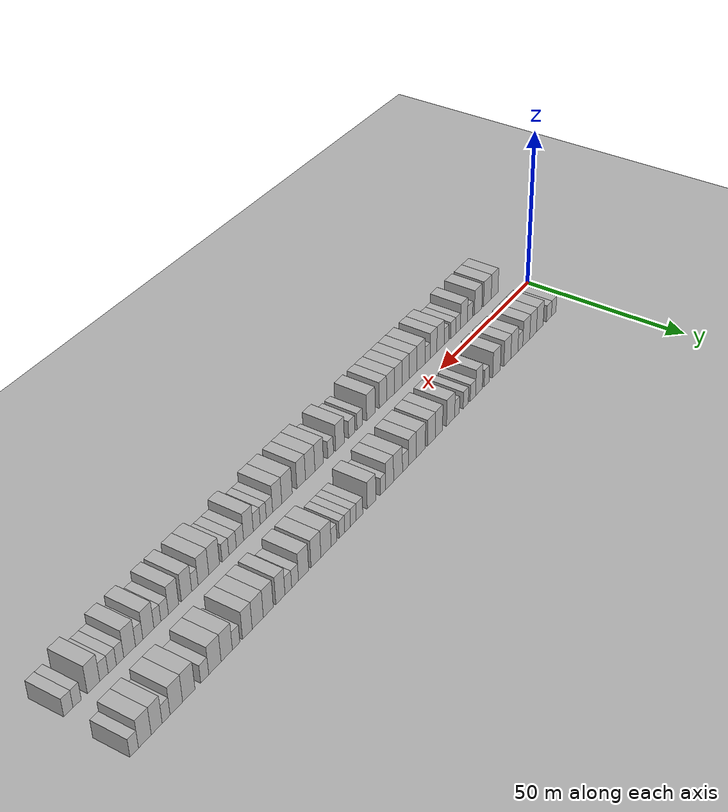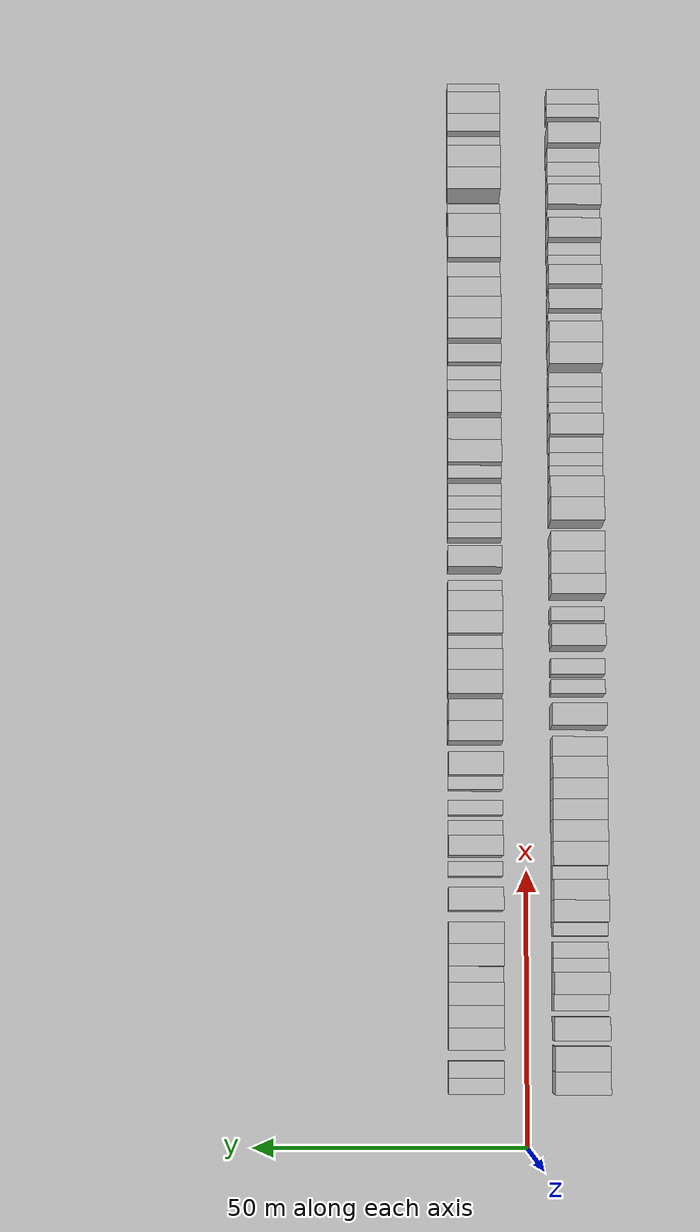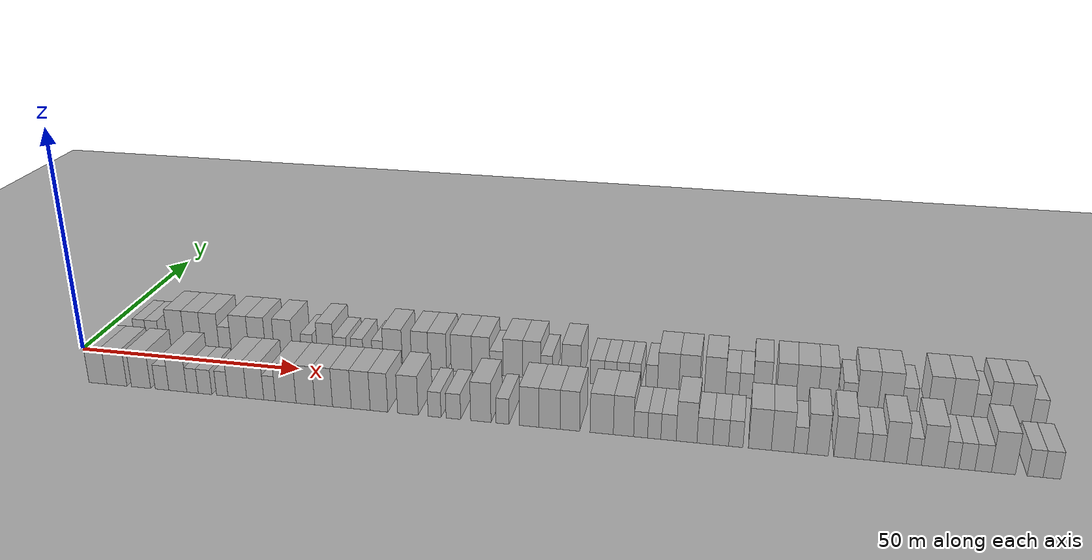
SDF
<?xml version="1.0" encoding="utf-8"?>

<sdf version="1.6">

   <world name="default">

      <gui fullscreen="0">

         <camera name="user_camera">

            <pose>-15 0 4.57585 0 0 0</pose>

            <view_controller>orbit</view_controller>

         </camera>

      </gui>

      <scene>

         <sky>

           <clouds>

             <speed>12</speed>

           </clouds>

         </sky>

         <ambient>0.4 0.4 0.4 1</ambient>

         <background>0.7 0.7 0.7 1</background>

         <shadows>1</shadows>

      </scene>

      <gravity>0 0 -9.8066</gravity>

      <magnetic_field>6e-06 2.3e-05 -4.2e-05</magnetic_field>

      <physics default="0" name="default_physics" type="ode">

         <ode>

            <solver>

               <type>quick</type>

               <iters>10</iters>

               <sor>1.0</sor>

               <use_dynamic_moi_rescaling>0</use_dynamic_moi_rescaling>

            </solver>

            <constraints>

               <cfm>0</cfm>

               <erp>0.2</erp>

               <contact_max_correcting_vel>100</contact_max_correcting_vel>

               <contact_surface_layer>0.001</contact_surface_layer>

            </constraints>

         </ode>

         <max_step_size>0.004</max_step_size>

         <real_time_factor>1</real_time_factor>

         <real_time_update_rate>250</real_time_update_rate>

      </physics>

      <light name="sun" type="directional">

         <cast_shadows>1</cast_shadows>

         <pose>0 0 10 0 0 0</pose>

         <diffuse>0.8 0.8 0.8 1</diffuse>

         <specular>0.2 0.2 0.2 1</specular>

         <attenuation>

            <range>1000</range>

            <constant>0.9</constant>

            <linear>0.01</linear>

            <quadratic>0.001</quadratic>

         </attenuation>

         <direction>-0.5 0.1 -0.9</direction>

      </light>

      <include>

         <name>ground_plane_1</name>

         <uri>model://HANNAS_ground_plane</uri>

         <pose>0 0 0  0 0 0</pose>

      </include>

      <include>

         <name>ground_plane_2</name>

         <uri>model://HANNAS_ground_plane</uri>

         <pose>100 0 0  0 0 0</pose>

      </include>

      <model name="building_1">

         <static>1</static>

         <pose frame="">11.4120 9.5000 0 0.000000 0.000000 1.570796</pose>

         <link name="link">

            <pose frame="">0 0 3.00 0 0 0</pose>

            <collision name="collision">

               <geometry>

                  <box>

                     <size>10.0000 2.8240 6.0000</size>

                  </box>

               </geometry>

               <max_contacts>10</max_contacts>

               <surface>

                  <contact>

                     <ode/>

                  </contact>

                  <bounce/>

                  <friction>

                     <torsional>

                        <ode/>

                     </torsional>

                     <ode/>

                  </friction>

               </surface>

            </collision>

            <visual name="visual">

               <cast_shadows>0</cast_shadows>

               <geometry>

                  <box>

                     <size>10.0000 2.8240 6.0000</size>

                  </box>

               </geometry>

               <material>

                  <script>

                     <uri>model://HANNAS_wall/materials/scripts</uri>

                     <uri>model://HANNAS_wall/materials/textures</uri>

                     <name>vrc/HANNAS_wall</name>

                  </script>

               </material>

            </visual>

            <self_collide>0</self_collide>

            <enable_wind>0</enable_wind>

            <kinematic>0</kinematic>

         </link>

      </model>

      <model name="building_2">

         <static>1</static>

         <pose frame="">14.3173 9.5000 0 0.000000 0.000000 1.570796</pose>

         <link name="link">

            <pose frame="">0 0 3.00 0 0 0</pose>

            <collision name="collision">

               <geometry>

                  <box>

                     <size>10.0000 2.9866 6.0000</size>

                  </box>

               </geometry>

               <max_contacts>10</max_contacts>

               <surface>

                  <contact>

                     <ode/>

                  </contact>

                  <bounce/>

                  <friction>

                     <torsional>

                        <ode/>

                     </torsional>

                     <ode/>

                  </friction>

               </surface>

            </collision>

            <visual name="visual">

               <cast_shadows>0</cast_shadows>

               <geometry>

                  <box>

                     <size>10.0000 2.9866 6.0000</size>

                  </box>

               </geometry>

               <material>

                  <script>

                     <uri>model://HANNAS_wall/materials/scripts</uri>

                     <uri>model://HANNAS_wall/materials/textures</uri>

                     <name>vrc/HANNAS_wall</name>

                  </script>

               </material>

            </visual>

            <self_collide>0</self_collide>

            <enable_wind>0</enable_wind>

            <kinematic>0</kinematic>

         </link>

      </model>

      <model name="building_3">

         <static>1</static>

         <pose frame="">19.8253 9.5000 0 0.000000 0.000000 1.570796</pose>

         <link name="link">

            <pose frame="">0 0 4.50 0 0 0</pose>

            <collision name="collision">

               <geometry>

                  <box>

                     <size>10.0000 4.0295 9.0000</size>

                  </box>

               </geometry>

               <max_contacts>10</max_contacts>

               <surface>

                  <contact>

                     <ode/>

                  </contact>

                  <bounce/>

                  <friction>

                     <torsional>

                        <ode/>

                     </torsional>

                     <ode/>

                  </friction>

               </surface>

            </collision>

            <visual name="visual">

               <cast_shadows>0</cast_shadows>

               <geometry>

                  <box>

                     <size>10.0000 4.0295 9.0000</size>

                  </box>

               </geometry>

               <material>

                  <script>

                     <uri>model://HANNAS_wall/materials/scripts</uri>

                     <uri>model://HANNAS_wall/materials/textures</uri>

                     <name>vrc/HANNAS_wall</name>

                  </script>

               </material>

            </visual>

            <self_collide>0</self_collide>

            <enable_wind>0</enable_wind>

            <kinematic>0</kinematic>

         </link>

      </model>

      <model name="building_4">

         <static>1</static>

         <pose frame="">23.8167 9.5000 0 0.000000 0.000000 1.570796</pose>

         <link name="link">

            <pose frame="">0 0 4.50 0 0 0</pose>

            <collision name="collision">

               <geometry>

                  <box>

                     <size>10.0000 3.9533 9.0000</size>

                  </box>

               </geometry>

               <max_contacts>10</max_contacts>

               <surface>

                  <contact>

                     <ode/>

                  </contact>

                  <bounce/>

                  <friction>

                     <torsional>

                        <ode/>

                     </torsional>

                     <ode/>

                  </friction>

               </surface>

            </collision>

            <visual name="visual">

               <cast_shadows>0</cast_shadows>

               <geometry>

                  <box>

                     <size>10.0000 3.9533 9.0000</size>

                  </box>

               </geometry>

               <material>

                  <script>

                     <uri>model://HANNAS_wall/materials/scripts</uri>

                     <uri>model://HANNAS_wall/materials/textures</uri>

                     <name>vrc/HANNAS_wall</name>

                  </script>

               </material>

            </visual>

            <self_collide>0</self_collide>

            <enable_wind>0</enable_wind>

            <kinematic>0</kinematic>

         </link>

      </model>

      <model name="building_5">

         <static>1</static>

         <pose frame="">27.8208 9.5000 0 0.000000 0.000000 1.570796</pose>

         <link name="link">

            <pose frame="">0 0 4.50 0 0 0</pose>

            <collision name="collision">

               <geometry>

                  <box>

                     <size>10.0000 4.0550 9.0000</size>

                  </box>

               </geometry>

               <max_contacts>10</max_contacts>

               <surface>

                  <contact>

                     <ode/>

                  </contact>

                  <bounce/>

                  <friction>

                     <torsional>

                        <ode/>

                     </torsional>

                     <ode/>

                  </friction>

               </surface>

            </collision>

            <visual name="visual">

               <cast_shadows>0</cast_shadows>

               <geometry>

                  <box>

                     <size>10.0000 4.0550 9.0000</size>

                  </box>

               </geometry>

               <material>

                  <script>

                     <uri>model://HANNAS_wall/materials/scripts</uri>

                     <uri>model://HANNAS_wall/materials/textures</uri>

                     <name>vrc/HANNAS_wall</name>

                  </script>

               </material>

            </visual>

            <self_collide>0</self_collide>

            <enable_wind>0</enable_wind>

            <kinematic>0</kinematic>

         </link>

      </model>

      <model name="building_6">

         <static>1</static>

         <pose frame="">31.2606 9.5000 0 0.000000 0.000000 1.570796</pose>

         <link name="link">

            <pose frame="">0 0 3.00 0 0 0</pose>

            <collision name="collision">

               <geometry>

                  <box>

                     <size>10.0000 2.8246 6.0000</size>

                  </box>

               </geometry>

               <max_contacts>10</max_contacts>

               <surface>

                  <contact>

                     <ode/>

                  </contact>

                  <bounce/>

                  <friction>

                     <torsional>

                        <ode/>

                     </torsional>

                     <ode/>

                  </friction>

               </surface>

            </collision>

            <visual name="visual">

               <cast_shadows>0</cast_shadows>

               <geometry>

                  <box>

                     <size>10.0000 2.8246 6.0000</size>

                  </box>

               </geometry>

               <material>

                  <script>

                     <uri>model://HANNAS_wall/materials/scripts</uri>

                     <uri>model://HANNAS_wall/materials/textures</uri>

                     <name>vrc/HANNAS_wall</name>

                  </script>

               </material>

            </visual>

            <self_collide>0</self_collide>

            <enable_wind>0</enable_wind>

            <kinematic>0</kinematic>

         </link>

      </model>

      <model name="building_7">

         <static>1</static>

         <pose frame="">34.7075 9.5000 0 0.000000 0.000000 1.570796</pose>

         <link name="link">

            <pose frame="">0 0 4.50 0 0 0</pose>

            <collision name="collision">

               <geometry>

                  <box>

                     <size>10.0000 4.0691 9.0000</size>

                  </box>

               </geometry>

               <max_contacts>10</max_contacts>

               <surface>

                  <contact>

                     <ode/>

                  </contact>

                  <bounce/>

                  <friction>

                     <torsional>

                        <ode/>

                     </torsional>

                     <ode/>

                  </friction>

               </surface>

            </collision>

            <visual name="visual">

               <cast_shadows>0</cast_shadows>

               <geometry>

                  <box>

                     <size>10.0000 4.0691 9.0000</size>

                  </box>

               </geometry>

               <material>

                  <script>

                     <uri>model://HANNAS_wall/materials/scripts</uri>

                     <uri>model://HANNAS_wall/materials/textures</uri>

                     <name>vrc/HANNAS_wall</name>

                  </script>

               </material>

            </visual>

            <self_collide>0</self_collide>

            <enable_wind>0</enable_wind>

            <kinematic>0</kinematic>

         </link>

      </model>

      <model name="building_8">

         <static>1</static>

         <pose frame="">38.6930 9.5000 0 0.000000 0.000000 1.570796</pose>

         <link name="link">

            <pose frame="">0 0 4.50 0 0 0</pose>

            <collision name="collision">

               <geometry>

                  <box>

                     <size>10.0000 3.9020 9.0000</size>

                  </box>

               </geometry>

               <max_contacts>10</max_contacts>

               <surface>

                  <contact>

                     <ode/>

                  </contact>

                  <bounce/>

                  <friction>

                     <torsional>

                        <ode/>

                     </torsional>

                     <ode/>

                  </friction>

               </surface>

            </collision>

            <visual name="visual">

               <cast_shadows>0</cast_shadows>

               <geometry>

                  <box>

                     <size>10.0000 3.9020 9.0000</size>

                  </box>

               </geometry>

               <material>

                  <script>

                     <uri>model://HANNAS_wall/materials/scripts</uri>

                     <uri>model://HANNAS_wall/materials/textures</uri>

                     <name>vrc/HANNAS_wall</name>

                  </script>

               </material>

            </visual>

            <self_collide>0</self_collide>

            <enable_wind>0</enable_wind>

            <kinematic>0</kinematic>

         </link>

      </model>

      <model name="building_9">

         <static>1</static>

         <pose frame="">44.7458 9.5000 0 0.000000 0.000000 1.570796</pose>

         <link name="link">

            <pose frame="">0 0 4.50 0 0 0</pose>

            <collision name="collision">

               <geometry>

                  <box>

                     <size>10.0000 4.2036 9.0000</size>

                  </box>

               </geometry>

               <max_contacts>10</max_contacts>

               <surface>

                  <contact>

                     <ode/>

                  </contact>

                  <bounce/>

                  <friction>

                     <torsional>

                        <ode/>

                     </torsional>

                     <ode/>

                  </friction>

               </surface>

            </collision>

            <visual name="visual">

               <cast_shadows>0</cast_shadows>

               <geometry>

                  <box>

                     <size>10.0000 4.2036 9.0000</size>

                  </box>

               </geometry>

               <material>

                  <script>

                     <uri>model://HANNAS_wall/materials/scripts</uri>

                     <uri>model://HANNAS_wall/materials/textures</uri>

                     <name>vrc/HANNAS_wall</name>

                  </script>

               </material>

            </visual>

            <self_collide>0</self_collide>

            <enable_wind>0</enable_wind>

            <kinematic>0</kinematic>

         </link>

      </model>

      <model name="building_10">

         <static>1</static>

         <pose frame="">50.1704 9.5000 0 0.000000 0.000000 1.570796</pose>

         <link name="link">

            <pose frame="">0 0 3.00 0 0 0</pose>

            <collision name="collision">

               <geometry>

                  <box>

                     <size>10.0000 2.6455 6.0000</size>

                  </box>

               </geometry>

               <max_contacts>10</max_contacts>

               <surface>

                  <contact>

                     <ode/>

                  </contact>

                  <bounce/>

                  <friction>

                     <torsional>

                        <ode/>

                     </torsional>

                     <ode/>

                  </friction>

               </surface>

            </collision>

            <visual name="visual">

               <cast_shadows>0</cast_shadows>

               <geometry>

                  <box>

                     <size>10.0000 2.6455 6.0000</size>

                  </box>

               </geometry>

               <material>

                  <script>

                     <uri>model://HANNAS_wall/materials/scripts</uri>

                     <uri>model://HANNAS_wall/materials/textures</uri>

                     <name>vrc/HANNAS_wall</name>

                  </script>

               </material>

            </visual>

            <self_collide>0</self_collide>

            <enable_wind>0</enable_wind>

            <kinematic>0</kinematic>

         </link>

      </model>

      <model name="building_11">

         <static>1</static>

         <pose frame="">54.3020 9.5000 0 0.000000 0.000000 1.570796</pose>

         <link name="link">

            <pose frame="">0 0 4.50 0 0 0</pose>

            <collision name="collision">

               <geometry>

                  <box>

                     <size>10.0000 3.6177 9.0000</size>

                  </box>

               </geometry>

               <max_contacts>10</max_contacts>

               <surface>

                  <contact>

                     <ode/>

                  </contact>

                  <bounce/>

                  <friction>

                     <torsional>

                        <ode/>

                     </torsional>

                     <ode/>

                  </friction>

               </surface>

            </collision>

            <visual name="visual">

               <cast_shadows>0</cast_shadows>

               <geometry>

                  <box>

                     <size>10.0000 3.6177 9.0000</size>

                  </box>

               </geometry>

               <material>

                  <script>

                     <uri>model://HANNAS_wall/materials/scripts</uri>

                     <uri>model://HANNAS_wall/materials/textures</uri>

                     <name>vrc/HANNAS_wall</name>

                  </script>

               </material>

            </visual>

            <self_collide>0</self_collide>

            <enable_wind>0</enable_wind>

            <kinematic>0</kinematic>

         </link>

      </model>

      <model name="building_12">

         <static>1</static>

         <pose frame="">57.5705 9.5000 0 0.000000 0.000000 1.570796</pose>

         <link name="link">

            <pose frame="">0 0 3.00 0 0 0</pose>

            <collision name="collision">

               <geometry>

                  <box>

                     <size>10.0000 2.9192 6.0000</size>

                  </box>

               </geometry>

               <max_contacts>10</max_contacts>

               <surface>

                  <contact>

                     <ode/>

                  </contact>

                  <bounce/>

                  <friction>

                     <torsional>

                        <ode/>

                     </torsional>

                     <ode/>

                  </friction>

               </surface>

            </collision>

            <visual name="visual">

               <cast_shadows>0</cast_shadows>

               <geometry>

                  <box>

                     <size>10.0000 2.9192 6.0000</size>

                  </box>

               </geometry>

               <material>

                  <script>

                     <uri>model://HANNAS_wall/materials/scripts</uri>

                     <uri>model://HANNAS_wall/materials/textures</uri>

                     <name>vrc/HANNAS_wall</name>

                  </script>

               </material>

            </visual>

            <self_collide>0</self_collide>

            <enable_wind>0</enable_wind>

            <kinematic>0</kinematic>

         </link>

      </model>

      <model name="building_13">

         <static>1</static>

         <pose frame="">61.3767 9.5000 0 0.000000 0.000000 1.570796</pose>

         <link name="link">

            <pose frame="">0 0 3.00 0 0 0</pose>

            <collision name="collision">

               <geometry>

                  <box>

                     <size>10.0000 2.6934 6.0000</size>

                  </box>

               </geometry>

               <max_contacts>10</max_contacts>

               <surface>

                  <contact>

                     <ode/>

                  </contact>

                  <bounce/>

                  <friction>

                     <torsional>

                        <ode/>

                     </torsional>

                     <ode/>

                  </friction>

               </surface>

            </collision>

            <visual name="visual">

               <cast_shadows>0</cast_shadows>

               <geometry>

                  <box>

                     <size>10.0000 2.6934 6.0000</size>

                  </box>

               </geometry>

               <material>

                  <script>

                     <uri>model://HANNAS_wall/materials/scripts</uri>

                     <uri>model://HANNAS_wall/materials/textures</uri>

                     <name>vrc/HANNAS_wall</name>

                  </script>

               </material>

            </visual>

            <self_collide>0</self_collide>

            <enable_wind>0</enable_wind>

            <kinematic>0</kinematic>

         </link>

      </model>

      <model name="building_14">

         <static>1</static>

         <pose frame="">65.9254 9.5000 0 0.000000 0.000000 1.570796</pose>

         <link name="link">

            <pose frame="">0 0 3.00 0 0 0</pose>

            <collision name="collision">

               <geometry>

                  <box>

                     <size>10.0000 2.4040 6.0000</size>

                  </box>

               </geometry>

               <max_contacts>10</max_contacts>

               <surface>

                  <contact>

                     <ode/>

                  </contact>

                  <bounce/>

                  <friction>

                     <torsional>

                        <ode/>

                     </torsional>

                     <ode/>

                  </friction>

               </surface>

            </collision>

            <visual name="visual">

               <cast_shadows>0</cast_shadows>

               <geometry>

                  <box>

                     <size>10.0000 2.4040 6.0000</size>

                  </box>

               </geometry>

               <material>

                  <script>

                     <uri>model://HANNAS_wall/materials/scripts</uri>

                     <uri>model://HANNAS_wall/materials/textures</uri>

                     <name>vrc/HANNAS_wall</name>

                  </script>

               </material>

            </visual>

            <self_collide>0</self_collide>

            <enable_wind>0</enable_wind>

            <kinematic>0</kinematic>

         </link>

      </model>

      <model name="building_15">

         <static>1</static>

         <pose frame="">69.2323 9.5000 0 0.000000 0.000000 1.570796</pose>

         <link name="link">

            <pose frame="">0 0 4.50 0 0 0</pose>

            <collision name="collision">

               <geometry>

                  <box>

                     <size>10.0000 4.2098 9.0000</size>

                  </box>

               </geometry>

               <max_contacts>10</max_contacts>

               <surface>

                  <contact>

                     <ode/>

                  </contact>

                  <bounce/>

                  <friction>

                     <torsional>

                        <ode/>

                     </torsional>

                     <ode/>

                  </friction>

               </surface>

            </collision>

            <visual name="visual">

               <cast_shadows>0</cast_shadows>

               <geometry>

                  <box>

                     <size>10.0000 4.2098 9.0000</size>

                  </box>

               </geometry>

               <material>

                  <script>

                     <uri>model://HANNAS_wall/materials/scripts</uri>

                     <uri>model://HANNAS_wall/materials/textures</uri>

                     <name>vrc/HANNAS_wall</name>

                  </script>

               </material>

            </visual>

            <self_collide>0</self_collide>

            <enable_wind>0</enable_wind>

            <kinematic>0</kinematic>

         </link>

      </model>

      <model name="building_16">

         <static>1</static>

         <pose frame="">75.1610 9.5000 0 0.000000 0.000000 1.570796</pose>

         <link name="link">

            <pose frame="">0 0 4.50 0 0 0</pose>

            <collision name="collision">

               <geometry>

                  <box>

                     <size>10.0000 3.6475 9.0000</size>

                  </box>

               </geometry>

               <max_contacts>10</max_contacts>

               <surface>

                  <contact>

                     <ode/>

                  </contact>

                  <bounce/>

                  <friction>

                     <torsional>

                        <ode/>

                     </torsional>

                     <ode/>

                  </friction>

               </surface>

            </collision>

            <visual name="visual">

               <cast_shadows>0</cast_shadows>

               <geometry>

                  <box>

                     <size>10.0000 3.6475 9.0000</size>

                  </box>

               </geometry>

               <material>

                  <script>

                     <uri>model://HANNAS_wall/materials/scripts</uri>

                     <uri>model://HANNAS_wall/materials/textures</uri>

                     <name>vrc/HANNAS_wall</name>

                  </script>

               </material>

            </visual>

            <self_collide>0</self_collide>

            <enable_wind>0</enable_wind>

            <kinematic>0</kinematic>

         </link>

      </model>

      <model name="building_17">

         <static>1</static>

         <pose frame="">78.9682 9.5000 0 0.000000 0.000000 1.570796</pose>

         <link name="link">

            <pose frame="">0 0 4.50 0 0 0</pose>

            <collision name="collision">

               <geometry>

                  <box>

                     <size>10.0000 3.9669 9.0000</size>

                  </box>

               </geometry>

               <max_contacts>10</max_contacts>

               <surface>

                  <contact>

                     <ode/>

                  </contact>

                  <bounce/>

                  <friction>

                     <torsional>

                        <ode/>

                     </torsional>

                     <ode/>

                  </friction>

               </surface>

            </collision>

            <visual name="visual">

               <cast_shadows>0</cast_shadows>

               <geometry>

                  <box>

                     <size>10.0000 3.9669 9.0000</size>

                  </box>

               </geometry>

               <material>

                  <script>

                     <uri>model://HANNAS_wall/materials/scripts</uri>

                     <uri>model://HANNAS_wall/materials/textures</uri>

                     <name>vrc/HANNAS_wall</name>

                  </script>

               </material>

            </visual>

            <self_collide>0</self_collide>

            <enable_wind>0</enable_wind>

            <kinematic>0</kinematic>

         </link>

      </model>

      <model name="building_18">

         <static>1</static>

         <pose frame="">84.1796 9.5000 0 0.000000 0.000000 1.570796</pose>

         <link name="link">

            <pose frame="">0 0 4.50 0 0 0</pose>

            <collision name="collision">

               <geometry>

                  <box>

                     <size>10.0000 4.4560 9.0000</size>

                  </box>

               </geometry>

               <max_contacts>10</max_contacts>

               <surface>

                  <contact>

                     <ode/>

                  </contact>

                  <bounce/>

                  <friction>

                     <torsional>

                        <ode/>

                     </torsional>

                     <ode/>

                  </friction>

               </surface>

            </collision>

            <visual name="visual">

               <cast_shadows>0</cast_shadows>

               <geometry>

                  <box>

                     <size>10.0000 4.4560 9.0000</size>

                  </box>

               </geometry>

               <material>

                  <script>

                     <uri>model://HANNAS_wall/materials/scripts</uri>

                     <uri>model://HANNAS_wall/materials/textures</uri>

                     <name>vrc/HANNAS_wall</name>

                  </script>

               </material>

            </visual>

            <self_collide>0</self_collide>

            <enable_wind>0</enable_wind>

            <kinematic>0</kinematic>

         </link>

      </model>

      <model name="building_19">

         <static>1</static>

         <pose frame="">88.3378 9.5000 0 0.000000 0.000000 1.570796</pose>

         <link name="link">

            <pose frame="">0 0 4.50 0 0 0</pose>

            <collision name="collision">

               <geometry>

                  <box>

                     <size>10.0000 3.8603 9.0000</size>

                  </box>

               </geometry>

               <max_contacts>10</max_contacts>

               <surface>

                  <contact>

                     <ode/>

                  </contact>

                  <bounce/>

                  <friction>

                     <torsional>

                        <ode/>

                     </torsional>

                     <ode/>

                  </friction>

               </surface>

            </collision>

            <visual name="visual">

               <cast_shadows>0</cast_shadows>

               <geometry>

                  <box>

                     <size>10.0000 3.8603 9.0000</size>

                  </box>

               </geometry>

               <material>

                  <script>

                     <uri>model://HANNAS_wall/materials/scripts</uri>

                     <uri>model://HANNAS_wall/materials/textures</uri>

                     <name>vrc/HANNAS_wall</name>

                  </script>

               </material>

            </visual>

            <self_collide>0</self_collide>

            <enable_wind>0</enable_wind>

            <kinematic>0</kinematic>

         </link>

      </model>

      <model name="building_20">

         <static>1</static>

         <pose frame="">91.6720 9.5000 0 0.000000 0.000000 1.570796</pose>

         <link name="link">

            <pose frame="">0 0 3.00 0 0 0</pose>

            <collision name="collision">

               <geometry>

                  <box>

                     <size>10.0000 2.8080 6.0000</size>

                  </box>

               </geometry>

               <max_contacts>10</max_contacts>

               <surface>

                  <contact>

                     <ode/>

                  </contact>

                  <bounce/>

                  <friction>

                     <torsional>

                        <ode/>

                     </torsional>

                     <ode/>

                  </friction>

               </surface>

            </collision>

            <visual name="visual">

               <cast_shadows>0</cast_shadows>

               <geometry>

                  <box>

                     <size>10.0000 2.8080 6.0000</size>

                  </box>

               </geometry>

               <material>

                  <script>

                     <uri>model://HANNAS_wall/materials/scripts</uri>

                     <uri>model://HANNAS_wall/materials/textures</uri>

                     <name>vrc/HANNAS_wall</name>

                  </script>

               </material>

            </visual>

            <self_collide>0</self_collide>

            <enable_wind>0</enable_wind>

            <kinematic>0</kinematic>

         </link>

      </model>

      <model name="building_21">

         <static>1</static>

         <pose frame="">95.1774 9.5000 0 0.000000 0.000000 1.570796</pose>

         <link name="link">

            <pose frame="">0 0 4.50 0 0 0</pose>

            <collision name="collision">

               <geometry>

                  <box>

                     <size>10.0000 4.2028 9.0000</size>

                  </box>

               </geometry>

               <max_contacts>10</max_contacts>

               <surface>

                  <contact>

                     <ode/>

                  </contact>

                  <bounce/>

                  <friction>

                     <torsional>

                        <ode/>

                     </torsional>

                     <ode/>

                  </friction>

               </surface>

            </collision>

            <visual name="visual">

               <cast_shadows>0</cast_shadows>

               <geometry>

                  <box>

                     <size>10.0000 4.2028 9.0000</size>

                  </box>

               </geometry>

               <material>

                  <script>

                     <uri>model://HANNAS_wall/materials/scripts</uri>

                     <uri>model://HANNAS_wall/materials/textures</uri>

                     <name>vrc/HANNAS_wall</name>

                  </script>

               </material>

            </visual>

            <self_collide>0</self_collide>

            <enable_wind>0</enable_wind>

            <kinematic>0</kinematic>

         </link>

      </model>

      <model name="building_22">

         <static>1</static>

         <pose frame="">99.1581 9.5000 0 0.000000 0.000000 1.570796</pose>

         <link name="link">

            <pose frame="">0 0 4.50 0 0 0</pose>

            <collision name="collision">

               <geometry>

                  <box>

                     <size>10.0000 3.7587 9.0000</size>

                  </box>

               </geometry>

               <max_contacts>10</max_contacts>

               <surface>

                  <contact>

                     <ode/>

                  </contact>

                  <bounce/>

                  <friction>

                     <torsional>

                        <ode/>

                     </torsional>

                     <ode/>

                  </friction>

               </surface>

            </collision>

            <visual name="visual">

               <cast_shadows>0</cast_shadows>

               <geometry>

                  <box>

                     <size>10.0000 3.7587 9.0000</size>

                  </box>

               </geometry>

               <material>

                  <script>

                     <uri>model://HANNAS_wall/materials/scripts</uri>

                     <uri>model://HANNAS_wall/materials/textures</uri>

                     <name>vrc/HANNAS_wall</name>

                  </script>

               </material>

            </visual>

            <self_collide>0</self_collide>

            <enable_wind>0</enable_wind>

            <kinematic>0</kinematic>

         </link>

      </model>

      <model name="building_23">

         <static>1</static>

         <pose frame="">102.2509 9.5000 0 0.000000 0.000000 1.570796</pose>

         <link name="link">

            <pose frame="">0 0 3.00 0 0 0</pose>

            <collision name="collision">

               <geometry>

                  <box>

                     <size>10.0000 2.4268 6.0000</size>

                  </box>

               </geometry>

               <max_contacts>10</max_contacts>

               <surface>

                  <contact>

                     <ode/>

                  </contact>

                  <bounce/>

                  <friction>

                     <torsional>

                        <ode/>

                     </torsional>

                     <ode/>

                  </friction>

               </surface>

            </collision>

            <visual name="visual">

               <cast_shadows>0</cast_shadows>

               <geometry>

                  <box>

                     <size>10.0000 2.4268 6.0000</size>

                  </box>

               </geometry>

               <material>

                  <script>

                     <uri>model://HANNAS_wall/materials/scripts</uri>

                     <uri>model://HANNAS_wall/materials/textures</uri>

                     <name>vrc/HANNAS_wall</name>

                  </script>

               </material>

            </visual>

            <self_collide>0</self_collide>

            <enable_wind>0</enable_wind>

            <kinematic>0</kinematic>

         </link>

      </model>

      <model name="building_24">

         <static>1</static>

         <pose frame="">107.4302 9.5000 0 0.000000 0.000000 1.570796</pose>

         <link name="link">

            <pose frame="">0 0 4.50 0 0 0</pose>

            <collision name="collision">

               <geometry>

                  <box>

                     <size>10.0000 3.9319 9.0000</size>

                  </box>

               </geometry>

               <max_contacts>10</max_contacts>

               <surface>

                  <contact>

                     <ode/>

                  </contact>

                  <bounce/>

                  <friction>

                     <torsional>

                        <ode/>

                     </torsional>

                     <ode/>

                  </friction>

               </surface>

            </collision>

            <visual name="visual">

               <cast_shadows>0</cast_shadows>

               <geometry>

                  <box>

                     <size>10.0000 3.9319 9.0000</size>

                  </box>

               </geometry>

               <material>

                  <script>

                     <uri>model://HANNAS_wall/materials/scripts</uri>

                     <uri>model://HANNAS_wall/materials/textures</uri>

                     <name>vrc/HANNAS_wall</name>

                  </script>

               </material>

            </visual>

            <self_collide>0</self_collide>

            <enable_wind>0</enable_wind>

            <kinematic>0</kinematic>

         </link>

      </model>

      <model name="building_25">

         <static>1</static>

         <pose frame="">112.8663 9.5000 0 0.000000 0.000000 1.570796</pose>

         <link name="link">

            <pose frame="">0 0 3.00 0 0 0</pose>

            <collision name="collision">

               <geometry>

                  <box>

                     <size>10.0000 2.9402 6.0000</size>

                  </box>

               </geometry>

               <max_contacts>10</max_contacts>

               <surface>

                  <contact>

                     <ode/>

                  </contact>

                  <bounce/>

                  <friction>

                     <torsional>

                        <ode/>

                     </torsional>

                     <ode/>

                  </friction>

               </surface>

            </collision>

            <visual name="visual">

               <cast_shadows>0</cast_shadows>

               <geometry>

                  <box>

                     <size>10.0000 2.9402 6.0000</size>

                  </box>

               </geometry>

               <material>

                  <script>

                     <uri>model://HANNAS_wall/materials/scripts</uri>

                     <uri>model://HANNAS_wall/materials/textures</uri>

                     <name>vrc/HANNAS_wall</name>

                  </script>

               </material>

            </visual>

            <self_collide>0</self_collide>

            <enable_wind>0</enable_wind>

            <kinematic>0</kinematic>

         </link>

      </model>

      <model name="building_26">

         <static>1</static>

         <pose frame="">115.5956 9.5000 0 0.000000 0.000000 1.570796</pose>

         <link name="link">

            <pose frame="">0 0 3.00 0 0 0</pose>

            <collision name="collision">

               <geometry>

                  <box>

                     <size>10.0000 2.5184 6.0000</size>

                  </box>

               </geometry>

               <max_contacts>10</max_contacts>

               <surface>

                  <contact>

                     <ode/>

                  </contact>

                  <bounce/>

                  <friction>

                     <torsional>

                        <ode/>

                     </torsional>

                     <ode/>

                  </friction>

               </surface>

            </collision>

            <visual name="visual">

               <cast_shadows>0</cast_shadows>

               <geometry>

                  <box>

                     <size>10.0000 2.5184 6.0000</size>

                  </box>

               </geometry>

               <material>

                  <script>

                     <uri>model://HANNAS_wall/materials/scripts</uri>

                     <uri>model://HANNAS_wall/materials/textures</uri>

                     <name>vrc/HANNAS_wall</name>

                  </script>

               </material>

            </visual>

            <self_collide>0</self_collide>

            <enable_wind>0</enable_wind>

            <kinematic>0</kinematic>

         </link>

      </model>

      <model name="building_27">

         <static>1</static>

         <pose frame="">118.1080 9.5000 0 0.000000 0.000000 1.570796</pose>

         <link name="link">

            <pose frame="">0 0 3.00 0 0 0</pose>

            <collision name="collision">

               <geometry>

                  <box>

                     <size>10.0000 2.5065 6.0000</size>

                  </box>

               </geometry>

               <max_contacts>10</max_contacts>

               <surface>

                  <contact>

                     <ode/>

                  </contact>

                  <bounce/>

                  <friction>

                     <torsional>

                        <ode/>

                     </torsional>

                     <ode/>

                  </friction>

               </surface>

            </collision>

            <visual name="visual">

               <cast_shadows>0</cast_shadows>

               <geometry>

                  <box>

                     <size>10.0000 2.5065 6.0000</size>

                  </box>

               </geometry>

               <material>

                  <script>

                     <uri>model://HANNAS_wall/materials/scripts</uri>

                     <uri>model://HANNAS_wall/materials/textures</uri>

                     <name>vrc/HANNAS_wall</name>

                  </script>

               </material>

            </visual>

            <self_collide>0</self_collide>

            <enable_wind>0</enable_wind>

            <kinematic>0</kinematic>

         </link>

      </model>

      <model name="building_28">

         <static>1</static>

         <pose frame="">120.5743 9.5000 0 0.000000 0.000000 1.570796</pose>

         <link name="link">

            <pose frame="">0 0 3.00 0 0 0</pose>

            <collision name="collision">

               <geometry>

                  <box>

                     <size>10.0000 2.4260 6.0000</size>

                  </box>

               </geometry>

               <max_contacts>10</max_contacts>

               <surface>

                  <contact>

                     <ode/>

                  </contact>

                  <bounce/>

                  <friction>

                     <torsional>

                        <ode/>

                     </torsional>

                     <ode/>

                  </friction>

               </surface>

            </collision>

            <visual name="visual">

               <cast_shadows>0</cast_shadows>

               <geometry>

                  <box>

                     <size>10.0000 2.4260 6.0000</size>

                  </box>

               </geometry>

               <material>

                  <script>

                     <uri>model://HANNAS_wall/materials/scripts</uri>

                     <uri>model://HANNAS_wall/materials/textures</uri>

                     <name>vrc/HANNAS_wall</name>

                  </script>

               </material>

            </visual>

            <self_collide>0</self_collide>

            <enable_wind>0</enable_wind>

            <kinematic>0</kinematic>

         </link>

      </model>

      <model name="building_29">

         <static>1</static>

         <pose frame="">123.9960 9.5000 0 0.000000 0.000000 1.570796</pose>

         <link name="link">

            <pose frame="">0 0 3.00 0 0 0</pose>

            <collision name="collision">

               <geometry>

                  <box>

                     <size>10.0000 2.4174 6.0000</size>

                  </box>

               </geometry>

               <max_contacts>10</max_contacts>

               <surface>

                  <contact>

                     <ode/>

                  </contact>

                  <bounce/>

                  <friction>

                     <torsional>

                        <ode/>

                     </torsional>

                     <ode/>

                  </friction>

               </surface>

            </collision>

            <visual name="visual">

               <cast_shadows>0</cast_shadows>

               <geometry>

                  <box>

                     <size>10.0000 2.4174 6.0000</size>

                  </box>

               </geometry>

               <material>

                  <script>

                     <uri>model://HANNAS_wall/materials/scripts</uri>

                     <uri>model://HANNAS_wall/materials/textures</uri>

                     <name>vrc/HANNAS_wall</name>

                  </script>

               </material>

            </visual>

            <self_collide>0</self_collide>

            <enable_wind>0</enable_wind>

            <kinematic>0</kinematic>

         </link>

      </model>

      <model name="building_30">

         <static>1</static>

         <pose frame="">127.3766 9.5000 0 0.000000 0.000000 1.570796</pose>

         <link name="link">

            <pose frame="">0 0 4.50 0 0 0</pose>

            <collision name="collision">

               <geometry>

                  <box>

                     <size>10.0000 4.3437 9.0000</size>

                  </box>

               </geometry>

               <max_contacts>10</max_contacts>

               <surface>

                  <contact>

                     <ode/>

                  </contact>

                  <bounce/>

                  <friction>

                     <torsional>

                        <ode/>

                     </torsional>

                     <ode/>

                  </friction>

               </surface>

            </collision>

            <visual name="visual">

               <cast_shadows>0</cast_shadows>

               <geometry>

                  <box>

                     <size>10.0000 4.3437 9.0000</size>

                  </box>

               </geometry>

               <material>

                  <script>

                     <uri>model://HANNAS_wall/materials/scripts</uri>

                     <uri>model://HANNAS_wall/materials/textures</uri>

                     <name>vrc/HANNAS_wall</name>

                  </script>

               </material>

            </visual>

            <self_collide>0</self_collide>

            <enable_wind>0</enable_wind>

            <kinematic>0</kinematic>

         </link>

      </model>

      <model name="building_31">

         <static>1</static>

         <pose frame="">131.6081 9.5000 0 0.000000 0.000000 1.570796</pose>

         <link name="link">

            <pose frame="">0 0 4.50 0 0 0</pose>

            <collision name="collision">

               <geometry>

                  <box>

                     <size>10.0000 4.1194 9.0000</size>

                  </box>

               </geometry>

               <max_contacts>10</max_contacts>

               <surface>

                  <contact>

                     <ode/>

                  </contact>

                  <bounce/>

                  <friction>

                     <torsional>

                        <ode/>

                     </torsional>

                     <ode/>

                  </friction>

               </surface>

            </collision>

            <visual name="visual">

               <cast_shadows>0</cast_shadows>

               <geometry>

                  <box>

                     <size>10.0000 4.1194 9.0000</size>

                  </box>

               </geometry>

               <material>

                  <script>

                     <uri>model://HANNAS_wall/materials/scripts</uri>

                     <uri>model://HANNAS_wall/materials/textures</uri>

                     <name>vrc/HANNAS_wall</name>

                  </script>

               </material>

            </visual>

            <self_collide>0</self_collide>

            <enable_wind>0</enable_wind>

            <kinematic>0</kinematic>

         </link>

      </model>

      <model name="building_32">

         <static>1</static>

         <pose frame="">136.7439 9.5000 0 0.000000 0.000000 1.570796</pose>

         <link name="link">

            <pose frame="">0 0 4.50 0 0 0</pose>

            <collision name="collision">

               <geometry>

                  <box>

                     <size>10.0000 4.1521 9.0000</size>

                  </box>

               </geometry>

               <max_contacts>10</max_contacts>

               <surface>

                  <contact>

                     <ode/>

                  </contact>

                  <bounce/>

                  <friction>

                     <torsional>

                        <ode/>

                     </torsional>

                     <ode/>

                  </friction>

               </surface>

            </collision>

            <visual name="visual">

               <cast_shadows>0</cast_shadows>

               <geometry>

                  <box>

                     <size>10.0000 4.1521 9.0000</size>

                  </box>

               </geometry>

               <material>

                  <script>

                     <uri>model://HANNAS_wall/materials/scripts</uri>

                     <uri>model://HANNAS_wall/materials/textures</uri>

                     <name>vrc/HANNAS_wall</name>

                  </script>

               </material>

            </visual>

            <self_collide>0</self_collide>

            <enable_wind>0</enable_wind>

            <kinematic>0</kinematic>

         </link>

      </model>

      <model name="building_33">

         <static>1</static>

         <pose frame="">140.2035 9.5000 0 0.000000 0.000000 1.570796</pose>

         <link name="link">

            <pose frame="">0 0 3.00 0 0 0</pose>

            <collision name="collision">

               <geometry>

                  <box>

                     <size>10.0000 2.7670 6.0000</size>

                  </box>

               </geometry>

               <max_contacts>10</max_contacts>

               <surface>

                  <contact>

                     <ode/>

                  </contact>

                  <bounce/>

                  <friction>

                     <torsional>

                        <ode/>

                     </torsional>

                     <ode/>

                  </friction>

               </surface>

            </collision>

            <visual name="visual">

               <cast_shadows>0</cast_shadows>

               <geometry>

                  <box>

                     <size>10.0000 2.7670 6.0000</size>

                  </box>

               </geometry>

               <material>

                  <script>

                     <uri>model://HANNAS_wall/materials/scripts</uri>

                     <uri>model://HANNAS_wall/materials/textures</uri>

                     <name>vrc/HANNAS_wall</name>

                  </script>

               </material>

            </visual>

            <self_collide>0</self_collide>

            <enable_wind>0</enable_wind>

            <kinematic>0</kinematic>

         </link>

      </model>

      <model name="building_34">

         <static>1</static>

         <pose frame="">142.9331 9.5000 0 0.000000 0.000000 1.570796</pose>

         <link name="link">

            <pose frame="">0 0 3.00 0 0 0</pose>

            <collision name="collision">

               <geometry>

                  <box>

                     <size>10.0000 2.6923 6.0000</size>

                  </box>

               </geometry>

               <max_contacts>10</max_contacts>

               <surface>

                  <contact>

                     <ode/>

                  </contact>

                  <bounce/>

                  <friction>

                     <torsional>

                        <ode/>

                     </torsional>

                     <ode/>

                  </friction>

               </surface>

            </collision>

            <visual name="visual">

               <cast_shadows>0</cast_shadows>

               <geometry>

                  <box>

                     <size>10.0000 2.6923 6.0000</size>

                  </box>

               </geometry>

               <material>

                  <script>

                     <uri>model://HANNAS_wall/materials/scripts</uri>

                     <uri>model://HANNAS_wall/materials/textures</uri>

                     <name>vrc/HANNAS_wall</name>

                  </script>

               </material>

            </visual>

            <self_collide>0</self_collide>

            <enable_wind>0</enable_wind>

            <kinematic>0</kinematic>

         </link>

      </model>

      <model name="building_35">

         <static>1</static>

         <pose frame="">146.0884 9.5000 0 0.000000 0.000000 1.570796</pose>

         <link name="link">

            <pose frame="">0 0 4.50 0 0 0</pose>

            <collision name="collision">

               <geometry>

                  <box>

                     <size>10.0000 3.6184 9.0000</size>

                  </box>

               </geometry>

               <max_contacts>10</max_contacts>

               <surface>

                  <contact>

                     <ode/>

                  </contact>

                  <bounce/>

                  <friction>

                     <torsional>

                        <ode/>

                     </torsional>

                     <ode/>

                  </friction>

               </surface>

            </collision>

            <visual name="visual">

               <cast_shadows>0</cast_shadows>

               <geometry>

                  <box>

                     <size>10.0000 3.6184 9.0000</size>

                  </box>

               </geometry>

               <material>

                  <script>

                     <uri>model://HANNAS_wall/materials/scripts</uri>

                     <uri>model://HANNAS_wall/materials/textures</uri>

                     <name>vrc/HANNAS_wall</name>

                  </script>

               </material>

            </visual>

            <self_collide>0</self_collide>

            <enable_wind>0</enable_wind>

            <kinematic>0</kinematic>

         </link>

      </model>

      <model name="building_36">

         <static>1</static>

         <pose frame="">150.8325 9.5000 0 0.000000 0.000000 1.570796</pose>

         <link name="link">

            <pose frame="">0 0 4.50 0 0 0</pose>

            <collision name="collision">

               <geometry>

                  <box>

                     <size>10.0000 3.8698 9.0000</size>

                  </box>

               </geometry>

               <max_contacts>10</max_contacts>

               <surface>

                  <contact>

                     <ode/>

                  </contact>

                  <bounce/>

                  <friction>

                     <torsional>

                        <ode/>

                     </torsional>

                     <ode/>

                  </friction>

               </surface>

            </collision>

            <visual name="visual">

               <cast_shadows>0</cast_shadows>

               <geometry>

                  <box>

                     <size>10.0000 3.8698 9.0000</size>

                  </box>

               </geometry>

               <material>

                  <script>

                     <uri>model://HANNAS_wall/materials/scripts</uri>

                     <uri>model://HANNAS_wall/materials/textures</uri>

                     <name>vrc/HANNAS_wall</name>

                  </script>

               </material>

            </visual>

            <self_collide>0</self_collide>

            <enable_wind>0</enable_wind>

            <kinematic>0</kinematic>

         </link>

      </model>

      <model name="building_37">

         <static>1</static>

         <pose frame="">154.8978 9.5000 0 0.000000 0.000000 1.570796</pose>

         <link name="link">

            <pose frame="">0 0 4.50 0 0 0</pose>

            <collision name="collision">

               <geometry>

                  <box>

                     <size>10.0000 4.2608 9.0000</size>

                  </box>

               </geometry>

               <max_contacts>10</max_contacts>

               <surface>

                  <contact>

                     <ode/>

                  </contact>

                  <bounce/>

                  <friction>

                     <torsional>

                        <ode/>

                     </torsional>

                     <ode/>

                  </friction>

               </surface>

            </collision>

            <visual name="visual">

               <cast_shadows>0</cast_shadows>

               <geometry>

                  <box>

                     <size>10.0000 4.2608 9.0000</size>

                  </box>

               </geometry>

               <material>

                  <script>

                     <uri>model://HANNAS_wall/materials/scripts</uri>

                     <uri>model://HANNAS_wall/materials/textures</uri>

                     <name>vrc/HANNAS_wall</name>

                  </script>

               </material>

            </visual>

            <self_collide>0</self_collide>

            <enable_wind>0</enable_wind>

            <kinematic>0</kinematic>

         </link>

      </model>

      <model name="building_38">

         <static>1</static>

         <pose frame="">158.8710 9.5000 0 0.000000 0.000000 1.570796</pose>

         <link name="link">

            <pose frame="">0 0 4.50 0 0 0</pose>

            <collision name="collision">

               <geometry>

                  <box>

                     <size>10.0000 3.6856 9.0000</size>

                  </box>

               </geometry>

               <max_contacts>10</max_contacts>

               <surface>

                  <contact>

                     <ode/>

                  </contact>

                  <bounce/>

                  <friction>

                     <torsional>

                        <ode/>

                     </torsional>

                     <ode/>

                  </friction>

               </surface>

            </collision>

            <visual name="visual">

               <cast_shadows>0</cast_shadows>

               <geometry>

                  <box>

                     <size>10.0000 3.6856 9.0000</size>

                  </box>

               </geometry>

               <material>

                  <script>

                     <uri>model://HANNAS_wall/materials/scripts</uri>

                     <uri>model://HANNAS_wall/materials/textures</uri>

                     <name>vrc/HANNAS_wall</name>

                  </script>

               </material>

            </visual>

            <self_collide>0</self_collide>

            <enable_wind>0</enable_wind>

            <kinematic>0</kinematic>

         </link>

      </model>

      <model name="building_39">

         <static>1</static>

         <pose frame="">163.0970 9.5000 0 0.000000 0.000000 1.570796</pose>

         <link name="link">

            <pose frame="">0 0 3.00 0 0 0</pose>

            <collision name="collision">

               <geometry>

                  <box>

                     <size>10.0000 2.7663 6.0000</size>

                  </box>

               </geometry>

               <max_contacts>10</max_contacts>

               <surface>

                  <contact>

                     <ode/>

                  </contact>

                  <bounce/>

                  <friction>

                     <torsional>

                        <ode/>

                     </torsional>

                     <ode/>

                  </friction>

               </surface>

            </collision>

            <visual name="visual">

               <cast_shadows>0</cast_shadows>

               <geometry>

                  <box>

                     <size>10.0000 2.7663 6.0000</size>

                  </box>

               </geometry>

               <material>

                  <script>

                     <uri>model://HANNAS_wall/materials/scripts</uri>

                     <uri>model://HANNAS_wall/materials/textures</uri>

                     <name>vrc/HANNAS_wall</name>

                  </script>

               </material>

            </visual>

            <self_collide>0</self_collide>

            <enable_wind>0</enable_wind>

            <kinematic>0</kinematic>

         </link>

      </model>

      <model name="building_40">

         <static>1</static>

         <pose frame="">166.5538 9.5000 0 0.000000 0.000000 1.570796</pose>

         <link name="link">

            <pose frame="">0 0 4.50 0 0 0</pose>

            <collision name="collision">

               <geometry>

                  <box>

                     <size>10.0000 4.1472 9.0000</size>

                  </box>

               </geometry>

               <max_contacts>10</max_contacts>

               <surface>

                  <contact>

                     <ode/>

                  </contact>

                  <bounce/>

                  <friction>

                     <torsional>

                        <ode/>

                     </torsional>

                     <ode/>

                  </friction>

               </surface>

            </collision>

            <visual name="visual">

               <cast_shadows>0</cast_shadows>

               <geometry>

                  <box>

                     <size>10.0000 4.1472 9.0000</size>

                  </box>

               </geometry>

               <material>

                  <script>

                     <uri>model://HANNAS_wall/materials/scripts</uri>

                     <uri>model://HANNAS_wall/materials/textures</uri>

                     <name>vrc/HANNAS_wall</name>

                  </script>

               </material>

            </visual>

            <self_collide>0</self_collide>

            <enable_wind>0</enable_wind>

            <kinematic>0</kinematic>

         </link>

      </model>

      <model name="building_41">

         <static>1</static>

         <pose frame="">170.8617 9.5000 0 0.000000 0.000000 1.570796</pose>

         <link name="link">

            <pose frame="">0 0 4.50 0 0 0</pose>

            <collision name="collision">

               <geometry>

                  <box>

                     <size>10.0000 4.4686 9.0000</size>

                  </box>

               </geometry>

               <max_contacts>10</max_contacts>

               <surface>

                  <contact>

                     <ode/>

                  </contact>

                  <bounce/>

                  <friction>

                     <torsional>

                        <ode/>

                     </torsional>

                     <ode/>

                  </friction>

               </surface>

            </collision>

            <visual name="visual">

               <cast_shadows>0</cast_shadows>

               <geometry>

                  <box>

                     <size>10.0000 4.4686 9.0000</size>

                  </box>

               </geometry>

               <material>

                  <script>

                     <uri>model://HANNAS_wall/materials/scripts</uri>

                     <uri>model://HANNAS_wall/materials/textures</uri>

                     <name>vrc/HANNAS_wall</name>

                  </script>

               </material>

            </visual>

            <self_collide>0</self_collide>

            <enable_wind>0</enable_wind>

            <kinematic>0</kinematic>

         </link>

      </model>

      <model name="building_42">

         <static>1</static>

         <pose frame="">174.5383 9.5000 0 0.000000 0.000000 1.570796</pose>

         <link name="link">

            <pose frame="">0 0 3.00 0 0 0</pose>

            <collision name="collision">

               <geometry>

                  <box>

                     <size>10.0000 2.8847 6.0000</size>

                  </box>

               </geometry>

               <max_contacts>10</max_contacts>

               <surface>

                  <contact>

                     <ode/>

                  </contact>

                  <bounce/>

                  <friction>

                     <torsional>

                        <ode/>

                     </torsional>

                     <ode/>

                  </friction>

               </surface>

            </collision>

            <visual name="visual">

               <cast_shadows>0</cast_shadows>

               <geometry>

                  <box>

                     <size>10.0000 2.8847 6.0000</size>

                  </box>

               </geometry>

               <material>

                  <script>

                     <uri>model://HANNAS_wall/materials/scripts</uri>

                     <uri>model://HANNAS_wall/materials/textures</uri>

                     <name>vrc/HANNAS_wall</name>

                  </script>

               </material>

            </visual>

            <self_collide>0</self_collide>

            <enable_wind>0</enable_wind>

            <kinematic>0</kinematic>

         </link>

      </model>

      <model name="building_43">

         <static>1</static>

         <pose frame="">180.1375 9.5000 0 0.000000 0.000000 1.570796</pose>

         <link name="link">

            <pose frame="">0 0 4.50 0 0 0</pose>

            <collision name="collision">

               <geometry>

                  <box>

                     <size>10.0000 4.3137 9.0000</size>

                  </box>

               </geometry>

               <max_contacts>10</max_contacts>

               <surface>

                  <contact>

                     <ode/>

                  </contact>

                  <bounce/>

                  <friction>

                     <torsional>

                        <ode/>

                     </torsional>

                     <ode/>

                  </friction>

               </surface>

            </collision>

            <visual name="visual">

               <cast_shadows>0</cast_shadows>

               <geometry>

                  <box>

                     <size>10.0000 4.3137 9.0000</size>

                  </box>

               </geometry>

               <material>

                  <script>

                     <uri>model://HANNAS_wall/materials/scripts</uri>

                     <uri>model://HANNAS_wall/materials/textures</uri>

                     <name>vrc/HANNAS_wall</name>

                  </script>

               </material>

            </visual>

            <self_collide>0</self_collide>

            <enable_wind>0</enable_wind>

            <kinematic>0</kinematic>

         </link>

      </model>

      <model name="building_44">

         <static>1</static>

         <pose frame="">184.4437 9.5000 0 0.000000 0.000000 1.570796</pose>

         <link name="link">

            <pose frame="">0 0 4.50 0 0 0</pose>

            <collision name="collision">

               <geometry>

                  <box>

                     <size>10.0000 4.2988 9.0000</size>

                  </box>

               </geometry>

               <max_contacts>10</max_contacts>

               <surface>

                  <contact>

                     <ode/>

                  </contact>

                  <bounce/>

                  <friction>

                     <torsional>

                        <ode/>

                     </torsional>

                     <ode/>

                  </friction>

               </surface>

            </collision>

            <visual name="visual">

               <cast_shadows>0</cast_shadows>

               <geometry>

                  <box>

                     <size>10.0000 4.2988 9.0000</size>

                  </box>

               </geometry>

               <material>

                  <script>

                     <uri>model://HANNAS_wall/materials/scripts</uri>

                     <uri>model://HANNAS_wall/materials/textures</uri>

                     <name>vrc/HANNAS_wall</name>

                  </script>

               </material>

            </visual>

            <self_collide>0</self_collide>

            <enable_wind>0</enable_wind>

            <kinematic>0</kinematic>

         </link>

      </model>

      <model name="building_45">

         <static>1</static>

         <pose frame="">187.9334 9.5000 0 0.000000 0.000000 1.570796</pose>

         <link name="link">

            <pose frame="">0 0 3.00 0 0 0</pose>

            <collision name="collision">

               <geometry>

                  <box>

                     <size>10.0000 2.6806 6.0000</size>

                  </box>

               </geometry>

               <max_contacts>10</max_contacts>

               <surface>

                  <contact>

                     <ode/>

                  </contact>

                  <bounce/>

                  <friction>

                     <torsional>

                        <ode/>

                     </torsional>

                     <ode/>

                  </friction>

               </surface>

            </collision>

            <visual name="visual">

               <cast_shadows>0</cast_shadows>

               <geometry>

                  <box>

                     <size>10.0000 2.6806 6.0000</size>

                  </box>

               </geometry>

               <material>

                  <script>

                     <uri>model://HANNAS_wall/materials/scripts</uri>

                     <uri>model://HANNAS_wall/materials/textures</uri>

                     <name>vrc/HANNAS_wall</name>

                  </script>

               </material>

            </visual>

            <self_collide>0</self_collide>

            <enable_wind>0</enable_wind>

            <kinematic>0</kinematic>

         </link>

      </model>

      <model name="building_46">

         <static>1</static>

         <pose frame="">191.0996 9.5000 0 0.000000 0.000000 1.570796</pose>

         <link name="link">

            <pose frame="">0 0 4.50 0 0 0</pose>

            <collision name="collision">

               <geometry>

                  <box>

                     <size>10.0000 3.6517 9.0000</size>

                  </box>

               </geometry>

               <max_contacts>10</max_contacts>

               <surface>

                  <contact>

                     <ode/>

                  </contact>

                  <bounce/>

                  <friction>

                     <torsional>

                        <ode/>

                     </torsional>

                     <ode/>

                  </friction>

               </surface>

            </collision>

            <visual name="visual">

               <cast_shadows>0</cast_shadows>

               <geometry>

                  <box>

                     <size>10.0000 3.6517 9.0000</size>

                  </box>

               </geometry>

               <material>

                  <script>

                     <uri>model://HANNAS_wall/materials/scripts</uri>

                     <uri>model://HANNAS_wall/materials/textures</uri>

                     <name>vrc/HANNAS_wall</name>

                  </script>

               </material>

            </visual>

            <self_collide>0</self_collide>

            <enable_wind>0</enable_wind>

            <kinematic>0</kinematic>

         </link>

      </model>

      <model name="building_47">

         <static>1</static>

         <pose frame="">195.0288 9.5000 0 0.000000 0.000000 1.570796</pose>

         <link name="link">

            <pose frame="">0 0 4.50 0 0 0</pose>

            <collision name="collision">

               <geometry>

                  <box>

                     <size>10.0000 4.2066 9.0000</size>

                  </box>

               </geometry>

               <max_contacts>10</max_contacts>

               <surface>

                  <contact>

                     <ode/>

                  </contact>

                  <bounce/>

                  <friction>

                     <torsional>

                        <ode/>

                     </torsional>

                     <ode/>

                  </friction>

               </surface>

            </collision>

            <visual name="visual">

               <cast_shadows>0</cast_shadows>

               <geometry>

                  <box>

                     <size>10.0000 4.2066 9.0000</size>

                  </box>

               </geometry>

               <material>

                  <script>

                     <uri>model://HANNAS_wall/materials/scripts</uri>

                     <uri>model://HANNAS_wall/materials/textures</uri>

                     <name>vrc/HANNAS_wall</name>

                  </script>

               </material>

            </visual>

            <self_collide>0</self_collide>

            <enable_wind>0</enable_wind>

            <kinematic>0</kinematic>

         </link>

      </model>

      <model name="building_48">

         <static>1</static>

         <pose frame="">198.5337 9.5000 0 0.000000 0.000000 1.570796</pose>

         <link name="link">

            <pose frame="">0 0 3.00 0 0 0</pose>

            <collision name="collision">

               <geometry>

                  <box>

                     <size>10.0000 2.8033 6.0000</size>

                  </box>

               </geometry>

               <max_contacts>10</max_contacts>

               <surface>

                  <contact>

                     <ode/>

                  </contact>

                  <bounce/>

                  <friction>

                     <torsional>

                        <ode/>

                     </torsional>

                     <ode/>

                  </friction>

               </surface>

            </collision>

            <visual name="visual">

               <cast_shadows>0</cast_shadows>

               <geometry>

                  <box>

                     <size>10.0000 2.8033 6.0000</size>

                  </box>

               </geometry>

               <material>

                  <script>

                     <uri>model://HANNAS_wall/materials/scripts</uri>

                     <uri>model://HANNAS_wall/materials/textures</uri>

                     <name>vrc/HANNAS_wall</name>

                  </script>

               </material>

            </visual>

            <self_collide>0</self_collide>

            <enable_wind>0</enable_wind>

            <kinematic>0</kinematic>

         </link>

      </model>

      <model name="building_49">

         <static>1</static>

         <pose frame="">12.0125 -9.5000 0 0.000000 0.000000 1.570796</pose>

         <link name="link">

            <pose frame="">0 0 4.50 0 0 0</pose>

            <collision name="collision">

               <geometry>

                  <box>

                     <size>10.0000 4.0250 9.0000</size>

                  </box>

               </geometry>

               <max_contacts>10</max_contacts>

               <surface>

                  <contact>

                     <ode/>

                  </contact>

                  <bounce/>

                  <friction>

                     <torsional>

                        <ode/>

                     </torsional>

                     <ode/>

                  </friction>

               </surface>

            </collision>

            <visual name="visual">

               <cast_shadows>0</cast_shadows>

               <geometry>

                  <box>

                     <size>10.0000 4.0250 9.0000</size>

                  </box>

               </geometry>

               <material>

                  <script>

                     <uri>model://HANNAS_wall/materials/scripts</uri>

                     <uri>model://HANNAS_wall/materials/textures</uri>

                     <name>vrc/HANNAS_wall</name>

                  </script>

               </material>

            </visual>

            <self_collide>0</self_collide>

            <enable_wind>0</enable_wind>

            <kinematic>0</kinematic>

         </link>

      </model>

      <model name="building_50">

         <static>1</static>

         <pose frame="">16.2547 -9.5000 0 0.000000 0.000000 1.570796</pose>

         <link name="link">

            <pose frame="">0 0 4.50 0 0 0</pose>

            <collision name="collision">

               <geometry>

                  <box>

                     <size>10.0000 4.4594 9.0000</size>

                  </box>

               </geometry>

               <max_contacts>10</max_contacts>

               <surface>

                  <contact>

                     <ode/>

                  </contact>

                  <bounce/>

                  <friction>

                     <torsional>

                        <ode/>

                     </torsional>

                     <ode/>

                  </friction>

               </surface>

            </collision>

            <visual name="visual">

               <cast_shadows>0</cast_shadows>

               <geometry>

                  <box>

                     <size>10.0000 4.4594 9.0000</size>

                  </box>

               </geometry>

               <material>

                  <script>

                     <uri>model://HANNAS_wall/materials/scripts</uri>

                     <uri>model://HANNAS_wall/materials/textures</uri>

                     <name>vrc/HANNAS_wall</name>

                  </script>

               </material>

            </visual>

            <self_collide>0</self_collide>

            <enable_wind>0</enable_wind>

            <kinematic>0</kinematic>

         </link>

      </model>

      <model name="building_51">

         <static>1</static>

         <pose frame="">21.6102 -9.5000 0 0.000000 0.000000 1.570796</pose>

         <link name="link">

            <pose frame="">0 0 4.50 0 0 0</pose>

            <collision name="collision">

               <geometry>

                  <box>

                     <size>10.0000 4.2515 9.0000</size>

                  </box>

               </geometry>

               <max_contacts>10</max_contacts>

               <surface>

                  <contact>

                     <ode/>

                  </contact>

                  <bounce/>

                  <friction>

                     <torsional>

                        <ode/>

                     </torsional>

                     <ode/>

                  </friction>

               </surface>

            </collision>

            <visual name="visual">

               <cast_shadows>0</cast_shadows>

               <geometry>

                  <box>

                     <size>10.0000 4.2515 9.0000</size>

                  </box>

               </geometry>

               <material>

                  <script>

                     <uri>model://HANNAS_wall/materials/scripts</uri>

                     <uri>model://HANNAS_wall/materials/textures</uri>

                     <name>vrc/HANNAS_wall</name>

                  </script>

               </material>

            </visual>

            <self_collide>0</self_collide>

            <enable_wind>0</enable_wind>

            <kinematic>0</kinematic>

         </link>

      </model>

      <model name="building_52">

         <static>1</static>

         <pose frame="">26.2296 -9.5000 0 0.000000 0.000000 1.570796</pose>

         <link name="link">

            <pose frame="">0 0 3.00 0 0 0</pose>

            <collision name="collision">

               <geometry>

                  <box>

                     <size>10.0000 2.9874 6.0000</size>

                  </box>

               </geometry>

               <max_contacts>10</max_contacts>

               <surface>

                  <contact>

                     <ode/>

                  </contact>

                  <bounce/>

                  <friction>

                     <torsional>

                        <ode/>

                     </torsional>

                     <ode/>

                  </friction>

               </surface>

            </collision>

            <visual name="visual">

               <cast_shadows>0</cast_shadows>

               <geometry>

                  <box>

                     <size>10.0000 2.9874 6.0000</size>

                  </box>

               </geometry>

               <material>

                  <script>

                     <uri>model://HANNAS_wall/materials/scripts</uri>

                     <uri>model://HANNAS_wall/materials/textures</uri>

                     <name>vrc/HANNAS_wall</name>

                  </script>

               </material>

            </visual>

            <self_collide>0</self_collide>

            <enable_wind>0</enable_wind>

            <kinematic>0</kinematic>

         </link>

      </model>

      <model name="building_53">

         <static>1</static>

         <pose frame="">29.6846 -9.5000 0 0.000000 0.000000 1.570796</pose>

         <link name="link">

            <pose frame="">0 0 4.50 0 0 0</pose>

            <collision name="collision">

               <geometry>

                  <box>

                     <size>10.0000 3.9226 9.0000</size>

                  </box>

               </geometry>

               <max_contacts>10</max_contacts>

               <surface>

                  <contact>

                     <ode/>

                  </contact>

                  <bounce/>

                  <friction>

                     <torsional>

                        <ode/>

                     </torsional>

                     <ode/>

                  </friction>

               </surface>

            </collision>

            <visual name="visual">

               <cast_shadows>0</cast_shadows>

               <geometry>

                  <box>

                     <size>10.0000 3.9226 9.0000</size>

                  </box>

               </geometry>

               <material>

                  <script>

                     <uri>model://HANNAS_wall/materials/scripts</uri>

                     <uri>model://HANNAS_wall/materials/textures</uri>

                     <name>vrc/HANNAS_wall</name>

                  </script>

               </material>

            </visual>

            <self_collide>0</self_collide>

            <enable_wind>0</enable_wind>

            <kinematic>0</kinematic>

         </link>

      </model>

      <model name="building_54">

         <static>1</static>

         <pose frame="">32.9074 -9.5000 0 0.000000 0.000000 1.570796</pose>

         <link name="link">

            <pose frame="">0 0 3.00 0 0 0</pose>

            <collision name="collision">

               <geometry>

                  <box>

                     <size>10.0000 2.5228 6.0000</size>

                  </box>

               </geometry>

               <max_contacts>10</max_contacts>

               <surface>

                  <contact>

                     <ode/>

                  </contact>

                  <bounce/>

                  <friction>

                     <torsional>

                        <ode/>

                     </torsional>

                     <ode/>

                  </friction>

               </surface>

            </collision>

            <visual name="visual">

               <cast_shadows>0</cast_shadows>

               <geometry>

                  <box>

                     <size>10.0000 2.5228 6.0000</size>

                  </box>

               </geometry>

               <material>

                  <script>

                     <uri>model://HANNAS_wall/materials/scripts</uri>

                     <uri>model://HANNAS_wall/materials/textures</uri>

                     <name>vrc/HANNAS_wall</name>

                  </script>

               </material>

            </visual>

            <self_collide>0</self_collide>

            <enable_wind>0</enable_wind>

            <kinematic>0</kinematic>

         </link>

      </model>

      <model name="building_55">

         <static>1</static>

         <pose frame="">35.6420 -9.5000 0 0.000000 0.000000 1.570796</pose>

         <link name="link">

            <pose frame="">0 0 3.00 0 0 0</pose>

            <collision name="collision">

               <geometry>

                  <box>

                     <size>10.0000 2.9465 6.0000</size>

                  </box>

               </geometry>

               <max_contacts>10</max_contacts>

               <surface>

                  <contact>

                     <ode/>

                  </contact>

                  <bounce/>

                  <friction>

                     <torsional>

                        <ode/>

                     </torsional>

                     <ode/>

                  </friction>

               </surface>

            </collision>

            <visual name="visual">

               <cast_shadows>0</cast_shadows>

               <geometry>

                  <box>

                     <size>10.0000 2.9465 6.0000</size>

                  </box>

               </geometry>

               <material>

                  <script>

                     <uri>model://HANNAS_wall/materials/scripts</uri>

                     <uri>model://HANNAS_wall/materials/textures</uri>

                     <name>vrc/HANNAS_wall</name>

                  </script>

               </material>

            </visual>

            <self_collide>0</self_collide>

            <enable_wind>0</enable_wind>

            <kinematic>0</kinematic>

         </link>

      </model>

      <model name="building_56">

         <static>1</static>

         <pose frame="">39.3429 -9.5000 0 0.000000 0.000000 1.570796</pose>

         <link name="link">

            <pose frame="">0 0 3.00 0 0 0</pose>

            <collision name="collision">

               <geometry>

                  <box>

                     <size>10.0000 2.4554 6.0000</size>

                  </box>

               </geometry>

               <max_contacts>10</max_contacts>

               <surface>

                  <contact>

                     <ode/>

                  </contact>

                  <bounce/>

                  <friction>

                     <torsional>

                        <ode/>

                     </torsional>

                     <ode/>

                  </friction>

               </surface>

            </collision>

            <visual name="visual">

               <cast_shadows>0</cast_shadows>

               <geometry>

                  <box>

                     <size>10.0000 2.4554 6.0000</size>

                  </box>

               </geometry>

               <material>

                  <script>

                     <uri>model://HANNAS_wall/materials/scripts</uri>

                     <uri>model://HANNAS_wall/materials/textures</uri>

                     <name>vrc/HANNAS_wall</name>

                  </script>

               </material>

            </visual>

            <self_collide>0</self_collide>

            <enable_wind>0</enable_wind>

            <kinematic>0</kinematic>

         </link>

      </model>

      <model name="building_57">

         <static>1</static>

         <pose frame="">42.5651 -9.5000 0 0.000000 0.000000 1.570796</pose>

         <link name="link">

            <pose frame="">0 0 4.50 0 0 0</pose>

            <collision name="collision">

               <geometry>

                  <box>

                     <size>10.0000 3.9889 9.0000</size>

                  </box>

               </geometry>

               <max_contacts>10</max_contacts>

               <surface>

                  <contact>

                     <ode/>

                  </contact>

                  <bounce/>

                  <friction>

                     <torsional>

                        <ode/>

                     </torsional>

                     <ode/>

                  </friction>

               </surface>

            </collision>

            <visual name="visual">

               <cast_shadows>0</cast_shadows>

               <geometry>

                  <box>

                     <size>10.0000 3.9889 9.0000</size>

                  </box>

               </geometry>

               <material>

                  <script>

                     <uri>model://HANNAS_wall/materials/scripts</uri>

                     <uri>model://HANNAS_wall/materials/textures</uri>

                     <name>vrc/HANNAS_wall</name>

                  </script>

               </material>

            </visual>

            <self_collide>0</self_collide>

            <enable_wind>0</enable_wind>

            <kinematic>0</kinematic>

         </link>

      </model>

      <model name="building_58">

         <static>1</static>

         <pose frame="">46.3990 -9.5000 0 0.000000 0.000000 1.570796</pose>

         <link name="link">

            <pose frame="">0 0 4.50 0 0 0</pose>

            <collision name="collision">

               <geometry>

                  <box>

                     <size>10.0000 3.6790 9.0000</size>

                  </box>

               </geometry>

               <max_contacts>10</max_contacts>

               <surface>

                  <contact>

                     <ode/>

                  </contact>

                  <bounce/>

                  <friction>

                     <torsional>

                        <ode/>

                     </torsional>

                     <ode/>

                  </friction>

               </surface>

            </collision>

            <visual name="visual">

               <cast_shadows>0</cast_shadows>

               <geometry>

                  <box>

                     <size>10.0000 3.6790 9.0000</size>

                  </box>

               </geometry>

               <material>

                  <script>

                     <uri>model://HANNAS_wall/materials/scripts</uri>

                     <uri>model://HANNAS_wall/materials/textures</uri>

                     <name>vrc/HANNAS_wall</name>

                  </script>

               </material>

            </visual>

            <self_collide>0</self_collide>

            <enable_wind>0</enable_wind>

            <kinematic>0</kinematic>

         </link>

      </model>

      <model name="building_59">

         <static>1</static>

         <pose frame="">49.4803 -9.5000 0 0.000000 0.000000 1.570796</pose>

         <link name="link">

            <pose frame="">0 0 3.00 0 0 0</pose>

            <collision name="collision">

               <geometry>

                  <box>

                     <size>10.0000 2.4836 6.0000</size>

                  </box>

               </geometry>

               <max_contacts>10</max_contacts>

               <surface>

                  <contact>

                     <ode/>

                  </contact>

                  <bounce/>

                  <friction>

                     <torsional>

                        <ode/>

                     </torsional>

                     <ode/>

                  </friction>

               </surface>

            </collision>

            <visual name="visual">

               <cast_shadows>0</cast_shadows>

               <geometry>

                  <box>

                     <size>10.0000 2.4836 6.0000</size>

                  </box>

               </geometry>

               <material>

                  <script>

                     <uri>model://HANNAS_wall/materials/scripts</uri>

                     <uri>model://HANNAS_wall/materials/textures</uri>

                     <name>vrc/HANNAS_wall</name>

                  </script>

               </material>

            </visual>

            <self_collide>0</self_collide>

            <enable_wind>0</enable_wind>

            <kinematic>0</kinematic>

         </link>

      </model>

      <model name="building_60">

         <static>1</static>

         <pose frame="">52.8970 -9.5000 0 0.000000 0.000000 1.570796</pose>

         <link name="link">

            <pose frame="">0 0 4.50 0 0 0</pose>

            <collision name="collision">

               <geometry>

                  <box>

                     <size>10.0000 4.3498 9.0000</size>

                  </box>

               </geometry>

               <max_contacts>10</max_contacts>

               <surface>

                  <contact>

                     <ode/>

                  </contact>

                  <bounce/>

                  <friction>

                     <torsional>

                        <ode/>

                     </torsional>

                     <ode/>

                  </friction>

               </surface>

            </collision>

            <visual name="visual">

               <cast_shadows>0</cast_shadows>

               <geometry>

                  <box>

                     <size>10.0000 4.3498 9.0000</size>

                  </box>

               </geometry>

               <material>

                  <script>

                     <uri>model://HANNAS_wall/materials/scripts</uri>

                     <uri>model://HANNAS_wall/materials/textures</uri>

                     <name>vrc/HANNAS_wall</name>

                  </script>

               </material>

            </visual>

            <self_collide>0</self_collide>

            <enable_wind>0</enable_wind>

            <kinematic>0</kinematic>

         </link>

      </model>

      <model name="building_61">

         <static>1</static>

         <pose frame="">57.0367 -9.5000 0 0.000000 0.000000 1.570796</pose>

         <link name="link">

            <pose frame="">0 0 4.50 0 0 0</pose>

            <collision name="collision">

               <geometry>

                  <box>

                     <size>10.0000 3.9296 9.0000</size>

                  </box>

               </geometry>

               <max_contacts>10</max_contacts>

               <surface>

                  <contact>

                     <ode/>

                  </contact>

                  <bounce/>

                  <friction>

                     <torsional>

                        <ode/>

                     </torsional>

                     <ode/>

                  </friction>

               </surface>

            </collision>

            <visual name="visual">

               <cast_shadows>0</cast_shadows>

               <geometry>

                  <box>

                     <size>10.0000 3.9296 9.0000</size>

                  </box>

               </geometry>

               <material>

                  <script>

                     <uri>model://HANNAS_wall/materials/scripts</uri>

                     <uri>model://HANNAS_wall/materials/textures</uri>

                     <name>vrc/HANNAS_wall</name>

                  </script>

               </material>

            </visual>

            <self_collide>0</self_collide>

            <enable_wind>0</enable_wind>

            <kinematic>0</kinematic>

         </link>

      </model>

      <model name="building_62">

         <static>1</static>

         <pose frame="">60.8553 -9.5000 0 0.000000 0.000000 1.570796</pose>

         <link name="link">

            <pose frame="">0 0 4.50 0 0 0</pose>

            <collision name="collision">

               <geometry>

                  <box>

                     <size>10.0000 3.7076 9.0000</size>

                  </box>

               </geometry>

               <max_contacts>10</max_contacts>

               <surface>

                  <contact>

                     <ode/>

                  </contact>

                  <bounce/>

                  <friction>

                     <torsional>

                        <ode/>

                     </torsional>

                     <ode/>

                  </friction>

               </surface>

            </collision>

            <visual name="visual">

               <cast_shadows>0</cast_shadows>

               <geometry>

                  <box>

                     <size>10.0000 3.7076 9.0000</size>

                  </box>

               </geometry>

               <material>

                  <script>

                     <uri>model://HANNAS_wall/materials/scripts</uri>

                     <uri>model://HANNAS_wall/materials/textures</uri>

                     <name>vrc/HANNAS_wall</name>

                  </script>

               </material>

            </visual>

            <self_collide>0</self_collide>

            <enable_wind>0</enable_wind>

            <kinematic>0</kinematic>

         </link>

      </model>

      <model name="building_63">

         <static>1</static>

         <pose frame="">64.6545 -9.5000 0 0.000000 0.000000 1.570796</pose>

         <link name="link">

            <pose frame="">0 0 4.50 0 0 0</pose>

            <collision name="collision">

               <geometry>

                  <box>

                     <size>10.0000 3.8907 9.0000</size>

                  </box>

               </geometry>

               <max_contacts>10</max_contacts>

               <surface>

                  <contact>

                     <ode/>

                  </contact>

                  <bounce/>

                  <friction>

                     <torsional>

                        <ode/>

                     </torsional>

                     <ode/>

                  </friction>

               </surface>

            </collision>

            <visual name="visual">

               <cast_shadows>0</cast_shadows>

               <geometry>

                  <box>

                     <size>10.0000 3.8907 9.0000</size>

                  </box>

               </geometry>

               <material>

                  <script>

                     <uri>model://HANNAS_wall/materials/scripts</uri>

                     <uri>model://HANNAS_wall/materials/textures</uri>

                     <name>vrc/HANNAS_wall</name>

                  </script>

               </material>

            </visual>

            <self_collide>0</self_collide>

            <enable_wind>0</enable_wind>

            <kinematic>0</kinematic>

         </link>

      </model>

      <model name="building_64">

         <static>1</static>

         <pose frame="">68.5563 -9.5000 0 0.000000 0.000000 1.570796</pose>

         <link name="link">

            <pose frame="">0 0 4.50 0 0 0</pose>

            <collision name="collision">

               <geometry>

                  <box>

                     <size>10.0000 3.9128 9.0000</size>

                  </box>

               </geometry>

               <max_contacts>10</max_contacts>

               <surface>

                  <contact>

                     <ode/>

                  </contact>

                  <bounce/>

                  <friction>

                     <torsional>

                        <ode/>

                     </torsional>

                     <ode/>

                  </friction>

               </surface>

            </collision>

            <visual name="visual">

               <cast_shadows>0</cast_shadows>

               <geometry>

                  <box>

                     <size>10.0000 3.9128 9.0000</size>

                  </box>

               </geometry>

               <material>

                  <script>

                     <uri>model://HANNAS_wall/materials/scripts</uri>

                     <uri>model://HANNAS_wall/materials/textures</uri>

                     <name>vrc/HANNAS_wall</name>

                  </script>

               </material>

            </visual>

            <self_collide>0</self_collide>

            <enable_wind>0</enable_wind>

            <kinematic>0</kinematic>

         </link>

      </model>

      <model name="building_65">

         <static>1</static>

         <pose frame="">72.3182 -9.5000 0 0.000000 0.000000 1.570796</pose>

         <link name="link">

            <pose frame="">0 0 4.50 0 0 0</pose>

            <collision name="collision">

               <geometry>

                  <box>

                     <size>10.0000 3.6110 9.0000</size>

                  </box>

               </geometry>

               <max_contacts>10</max_contacts>

               <surface>

                  <contact>

                     <ode/>

                  </contact>

                  <bounce/>

                  <friction>

                     <torsional>

                        <ode/>

                     </torsional>

                     <ode/>

                  </friction>

               </surface>

            </collision>

            <visual name="visual">

               <cast_shadows>0</cast_shadows>

               <geometry>

                  <box>

                     <size>10.0000 3.6110 9.0000</size>

                  </box>

               </geometry>

               <material>

                  <script>

                     <uri>model://HANNAS_wall/materials/scripts</uri>

                     <uri>model://HANNAS_wall/materials/textures</uri>

                     <name>vrc/HANNAS_wall</name>

                  </script>

               </material>

            </visual>

            <self_collide>0</self_collide>

            <enable_wind>0</enable_wind>

            <kinematic>0</kinematic>

         </link>

      </model>

      <model name="building_66">

         <static>1</static>

         <pose frame="">78.2149 -9.5000 0 0.000000 0.000000 1.570796</pose>

         <link name="link">

            <pose frame="">0 0 4.50 0 0 0</pose>

            <collision name="collision">

               <geometry>

                  <box>

                     <size>10.0000 4.1823 9.0000</size>

                  </box>

               </geometry>

               <max_contacts>10</max_contacts>

               <surface>

                  <contact>

                     <ode/>

                  </contact>

                  <bounce/>

                  <friction>

                     <torsional>

                        <ode/>

                     </torsional>

                     <ode/>

                  </friction>

               </surface>

            </collision>

            <visual name="visual">

               <cast_shadows>0</cast_shadows>

               <geometry>

                  <box>

                     <size>10.0000 4.1823 9.0000</size>

                  </box>

               </geometry>

               <material>

                  <script>

                     <uri>model://HANNAS_wall/materials/scripts</uri>

                     <uri>model://HANNAS_wall/materials/textures</uri>

                     <name>vrc/HANNAS_wall</name>

                  </script>

               </material>

            </visual>

            <self_collide>0</self_collide>

            <enable_wind>0</enable_wind>

            <kinematic>0</kinematic>

         </link>

      </model>

      <model name="building_67">

         <static>1</static>

         <pose frame="">83.6147 -9.5000 0 0.000000 0.000000 1.570796</pose>

         <link name="link">

            <pose frame="">0 0 3.00 0 0 0</pose>

            <collision name="collision">

               <geometry>

                  <box>

                     <size>10.0000 2.6173 6.0000</size>

                  </box>

               </geometry>

               <max_contacts>10</max_contacts>

               <surface>

                  <contact>

                     <ode/>

                  </contact>

                  <bounce/>

                  <friction>

                     <torsional>

                        <ode/>

                     </torsional>

                     <ode/>

                  </friction>

               </surface>

            </collision>

            <visual name="visual">

               <cast_shadows>0</cast_shadows>

               <geometry>

                  <box>

                     <size>10.0000 2.6173 6.0000</size>

                  </box>

               </geometry>

               <material>

                  <script>

                     <uri>model://HANNAS_wall/materials/scripts</uri>

                     <uri>model://HANNAS_wall/materials/textures</uri>

                     <name>vrc/HANNAS_wall</name>

                  </script>

               </material>

            </visual>

            <self_collide>0</self_collide>

            <enable_wind>0</enable_wind>

            <kinematic>0</kinematic>

         </link>

      </model>

      <model name="building_68">

         <static>1</static>

         <pose frame="">87.3883 -9.5000 0 0.000000 0.000000 1.570796</pose>

         <link name="link">

            <pose frame="">0 0 3.00 0 0 0</pose>

            <collision name="collision">

               <geometry>

                  <box>

                     <size>10.0000 2.9300 6.0000</size>

                  </box>

               </geometry>

               <max_contacts>10</max_contacts>

               <surface>

                  <contact>

                     <ode/>

                  </contact>

                  <bounce/>

                  <friction>

                     <torsional>

                        <ode/>

                     </torsional>

                     <ode/>

                  </friction>

               </surface>

            </collision>

            <visual name="visual">

               <cast_shadows>0</cast_shadows>

               <geometry>

                  <box>

                     <size>10.0000 2.9300 6.0000</size>

                  </box>

               </geometry>

               <material>

                  <script>

                     <uri>model://HANNAS_wall/materials/scripts</uri>

                     <uri>model://HANNAS_wall/materials/textures</uri>

                     <name>vrc/HANNAS_wall</name>

                  </script>

               </material>

            </visual>

            <self_collide>0</self_collide>

            <enable_wind>0</enable_wind>

            <kinematic>0</kinematic>

         </link>

      </model>

      <model name="building_69">

         <static>1</static>

         <pose frame="">92.8749 -9.5000 0 0.000000 0.000000 1.570796</pose>

         <link name="link">

            <pose frame="">0 0 4.50 0 0 0</pose>

            <collision name="collision">

               <geometry>

                  <box>

                     <size>10.0000 4.0431 9.0000</size>

                  </box>

               </geometry>

               <max_contacts>10</max_contacts>

               <surface>

                  <contact>

                     <ode/>

                  </contact>

                  <bounce/>

                  <friction>

                     <torsional>

                        <ode/>

                     </torsional>

                     <ode/>

                  </friction>

               </surface>

            </collision>

            <visual name="visual">

               <cast_shadows>0</cast_shadows>

               <geometry>

                  <box>

                     <size>10.0000 4.0431 9.0000</size>

                  </box>

               </geometry>

               <material>

                  <script>

                     <uri>model://HANNAS_wall/materials/scripts</uri>

                     <uri>model://HANNAS_wall/materials/textures</uri>

                     <name>vrc/HANNAS_wall</name>

                  </script>

               </material>

            </visual>

            <self_collide>0</self_collide>

            <enable_wind>0</enable_wind>

            <kinematic>0</kinematic>

         </link>

      </model>

      <model name="building_70">

         <static>1</static>

         <pose frame="">97.1820 -9.5000 0 0.000000 0.000000 1.570796</pose>

         <link name="link">

            <pose frame="">0 0 3.00 0 0 0</pose>

            <collision name="collision">

               <geometry>

                  <box>

                     <size>10.0000 2.5712 6.0000</size>

                  </box>

               </geometry>

               <max_contacts>10</max_contacts>

               <surface>

                  <contact>

                     <ode/>

                  </contact>

                  <bounce/>

                  <friction>

                     <torsional>

                        <ode/>

                     </torsional>

                     <ode/>

                  </friction>

               </surface>

            </collision>

            <visual name="visual">

               <cast_shadows>0</cast_shadows>

               <geometry>

                  <box>

                     <size>10.0000 2.5712 6.0000</size>

                  </box>

               </geometry>

               <material>

                  <script>

                     <uri>model://HANNAS_wall/materials/scripts</uri>

                     <uri>model://HANNAS_wall/materials/textures</uri>

                     <name>vrc/HANNAS_wall</name>

                  </script>

               </material>

            </visual>

            <self_collide>0</self_collide>

            <enable_wind>0</enable_wind>

            <kinematic>0</kinematic>

         </link>

      </model>

      <model name="building_71">

         <static>1</static>

         <pose frame="">102.3761 -9.5000 0 0.000000 0.000000 1.570796</pose>

         <link name="link">

            <pose frame="">0 0 4.50 0 0 0</pose>

            <collision name="collision">

               <geometry>

                  <box>

                     <size>10.0000 3.8168 9.0000</size>

                  </box>

               </geometry>

               <max_contacts>10</max_contacts>

               <surface>

                  <contact>

                     <ode/>

                  </contact>

                  <bounce/>

                  <friction>

                     <torsional>

                        <ode/>

                     </torsional>

                     <ode/>

                  </friction>

               </surface>

            </collision>

            <visual name="visual">

               <cast_shadows>0</cast_shadows>

               <geometry>

                  <box>

                     <size>10.0000 3.8168 9.0000</size>

                  </box>

               </geometry>

               <material>

                  <script>

                     <uri>model://HANNAS_wall/materials/scripts</uri>

                     <uri>model://HANNAS_wall/materials/textures</uri>

                     <name>vrc/HANNAS_wall</name>

                  </script>

               </material>

            </visual>

            <self_collide>0</self_collide>

            <enable_wind>0</enable_wind>

            <kinematic>0</kinematic>

         </link>

      </model>

      <model name="building_72">

         <static>1</static>

         <pose frame="">106.3669 -9.5000 0 0.000000 0.000000 1.570796</pose>

         <link name="link">

            <pose frame="">0 0 4.50 0 0 0</pose>

            <collision name="collision">

               <geometry>

                  <box>

                     <size>10.0000 4.1648 9.0000</size>

                  </box>

               </geometry>

               <max_contacts>10</max_contacts>

               <surface>

                  <contact>

                     <ode/>

                  </contact>

                  <bounce/>

                  <friction>

                     <torsional>

                        <ode/>

                     </torsional>

                     <ode/>

                  </friction>

               </surface>

            </collision>

            <visual name="visual">

               <cast_shadows>0</cast_shadows>

               <geometry>

                  <box>

                     <size>10.0000 4.1648 9.0000</size>

                  </box>

               </geometry>

               <material>

                  <script>

                     <uri>model://HANNAS_wall/materials/scripts</uri>

                     <uri>model://HANNAS_wall/materials/textures</uri>

                     <name>vrc/HANNAS_wall</name>

                  </script>

               </material>

            </visual>

            <self_collide>0</self_collide>

            <enable_wind>0</enable_wind>

            <kinematic>0</kinematic>

         </link>

      </model>

      <model name="building_73">

         <static>1</static>

         <pose frame="">110.3328 -9.5000 0 0.000000 0.000000 1.570796</pose>

         <link name="link">

            <pose frame="">0 0 4.50 0 0 0</pose>

            <collision name="collision">

               <geometry>

                  <box>

                     <size>10.0000 3.7671 9.0000</size>

                  </box>

               </geometry>

               <max_contacts>10</max_contacts>

               <surface>

                  <contact>

                     <ode/>

                  </contact>

                  <bounce/>

                  <friction>

                     <torsional>

                        <ode/>

                     </torsional>

                     <ode/>

                  </friction>

               </surface>

            </collision>

            <visual name="visual">

               <cast_shadows>0</cast_shadows>

               <geometry>

                  <box>

                     <size>10.0000 3.7671 9.0000</size>

                  </box>

               </geometry>

               <material>

                  <script>

                     <uri>model://HANNAS_wall/materials/scripts</uri>

                     <uri>model://HANNAS_wall/materials/textures</uri>

                     <name>vrc/HANNAS_wall</name>

                  </script>

               </material>

            </visual>

            <self_collide>0</self_collide>

            <enable_wind>0</enable_wind>

            <kinematic>0</kinematic>

         </link>

      </model>

      <model name="building_74">

         <static>1</static>

         <pose frame="">116.4520 -9.5000 0 0.000000 0.000000 1.570796</pose>

         <link name="link">

            <pose frame="">0 0 4.50 0 0 0</pose>

            <collision name="collision">

               <geometry>

                  <box>

                     <size>10.0000 4.4713 9.0000</size>

                  </box>

               </geometry>

               <max_contacts>10</max_contacts>

               <surface>

                  <contact>

                     <ode/>

                  </contact>

                  <bounce/>

                  <friction>

                     <torsional>

                        <ode/>

                     </torsional>

                     <ode/>

                  </friction>

               </surface>

            </collision>

            <visual name="visual">

               <cast_shadows>0</cast_shadows>

               <geometry>

                  <box>

                     <size>10.0000 4.4713 9.0000</size>

                  </box>

               </geometry>

               <material>

                  <script>

                     <uri>model://HANNAS_wall/materials/scripts</uri>

                     <uri>model://HANNAS_wall/materials/textures</uri>

                     <name>vrc/HANNAS_wall</name>

                  </script>

               </material>

            </visual>

            <self_collide>0</self_collide>

            <enable_wind>0</enable_wind>

            <kinematic>0</kinematic>

         </link>

      </model>

      <model name="building_75">

         <static>1</static>

         <pose frame="">120.6215 -9.5000 0 0.000000 0.000000 1.570796</pose>

         <link name="link">

            <pose frame="">0 0 4.50 0 0 0</pose>

            <collision name="collision">

               <geometry>

                  <box>

                     <size>10.0000 3.8678 9.0000</size>

                  </box>

               </geometry>

               <max_contacts>10</max_contacts>

               <surface>

                  <contact>

                     <ode/>

                  </contact>

                  <bounce/>

                  <friction>

                     <torsional>

                        <ode/>

                     </torsional>

                     <ode/>

                  </friction>

               </surface>

            </collision>

            <visual name="visual">

               <cast_shadows>0</cast_shadows>

               <geometry>

                  <box>

                     <size>10.0000 3.8678 9.0000</size>

                  </box>

               </geometry>

               <material>

                  <script>

                     <uri>model://HANNAS_wall/materials/scripts</uri>

                     <uri>model://HANNAS_wall/materials/textures</uri>

                     <name>vrc/HANNAS_wall</name>

                  </script>

               </material>

            </visual>

            <self_collide>0</self_collide>

            <enable_wind>0</enable_wind>

            <kinematic>0</kinematic>

         </link>

      </model>

      <model name="building_76">

         <static>1</static>

         <pose frame="">123.8800 -9.5000 0 0.000000 0.000000 1.570796</pose>

         <link name="link">

            <pose frame="">0 0 3.00 0 0 0</pose>

            <collision name="collision">

               <geometry>

                  <box>

                     <size>10.0000 2.6493 6.0000</size>

                  </box>

               </geometry>

               <max_contacts>10</max_contacts>

               <surface>

                  <contact>

                     <ode/>

                  </contact>

                  <bounce/>

                  <friction>

                     <torsional>

                        <ode/>

                     </torsional>

                     <ode/>

                  </friction>

               </surface>

            </collision>

            <visual name="visual">

               <cast_shadows>0</cast_shadows>

               <geometry>

                  <box>

                     <size>10.0000 2.6493 6.0000</size>

                  </box>

               </geometry>

               <material>

                  <script>

                     <uri>model://HANNAS_wall/materials/scripts</uri>

                     <uri>model://HANNAS_wall/materials/textures</uri>

                     <name>vrc/HANNAS_wall</name>

                  </script>

               </material>

            </visual>

            <self_collide>0</self_collide>

            <enable_wind>0</enable_wind>

            <kinematic>0</kinematic>

         </link>

      </model>

      <model name="building_77">

         <static>1</static>

         <pose frame="">126.4538 -9.5000 0 0.000000 0.000000 1.570796</pose>

         <link name="link">

            <pose frame="">0 0 3.00 0 0 0</pose>

            <collision name="collision">

               <geometry>

                  <box>

                     <size>10.0000 2.4983 6.0000</size>

                  </box>

               </geometry>

               <max_contacts>10</max_contacts>

               <surface>

                  <contact>

                     <ode/>

                  </contact>

                  <bounce/>

                  <friction>

                     <torsional>

                        <ode/>

                     </torsional>

                     <ode/>

                  </friction>

               </surface>

            </collision>

            <visual name="visual">

               <cast_shadows>0</cast_shadows>

               <geometry>

                  <box>

                     <size>10.0000 2.4983 6.0000</size>

                  </box>

               </geometry>

               <material>

                  <script>

                     <uri>model://HANNAS_wall/materials/scripts</uri>

                     <uri>model://HANNAS_wall/materials/textures</uri>

                     <name>vrc/HANNAS_wall</name>

                  </script>

               </material>

            </visual>

            <self_collide>0</self_collide>

            <enable_wind>0</enable_wind>

            <kinematic>0</kinematic>

         </link>

      </model>

      <model name="building_78">

         <static>1</static>

         <pose frame="">129.1369 -9.5000 0 0.000000 0.000000 1.570796</pose>

         <link name="link">

            <pose frame="">0 0 3.00 0 0 0</pose>

            <collision name="collision">

               <geometry>

                  <box>

                     <size>10.0000 2.8678 6.0000</size>

                  </box>

               </geometry>

               <max_contacts>10</max_contacts>

               <surface>

                  <contact>

                     <ode/>

                  </contact>

                  <bounce/>

                  <friction>

                     <torsional>

                        <ode/>

                     </torsional>

                     <ode/>

                  </friction>

               </surface>

            </collision>

            <visual name="visual">

               <cast_shadows>0</cast_shadows>

               <geometry>

                  <box>

                     <size>10.0000 2.8678 6.0000</size>

                  </box>

               </geometry>

               <material>

                  <script>

                     <uri>model://HANNAS_wall/materials/scripts</uri>

                     <uri>model://HANNAS_wall/materials/textures</uri>

                     <name>vrc/HANNAS_wall</name>

                  </script>

               </material>

            </visual>

            <self_collide>0</self_collide>

            <enable_wind>0</enable_wind>

            <kinematic>0</kinematic>

         </link>

      </model>

      <model name="building_79">

         <static>1</static>

         <pose frame="">132.5157 -9.5000 0 0.000000 0.000000 1.570796</pose>

         <link name="link">

            <pose frame="">0 0 4.50 0 0 0</pose>

            <collision name="collision">

               <geometry>

                  <box>

                     <size>10.0000 3.8898 9.0000</size>

                  </box>

               </geometry>

               <max_contacts>10</max_contacts>

               <surface>

                  <contact>

                     <ode/>

                  </contact>

                  <bounce/>

                  <friction>

                     <torsional>

                        <ode/>

                     </torsional>

                     <ode/>

                  </friction>

               </surface>

            </collision>

            <visual name="visual">

               <cast_shadows>0</cast_shadows>

               <geometry>

                  <box>

                     <size>10.0000 3.8898 9.0000</size>

                  </box>

               </geometry>

               <material>

                  <script>

                     <uri>model://HANNAS_wall/materials/scripts</uri>

                     <uri>model://HANNAS_wall/materials/textures</uri>

                     <name>vrc/HANNAS_wall</name>

                  </script>

               </material>

            </visual>

            <self_collide>0</self_collide>

            <enable_wind>0</enable_wind>

            <kinematic>0</kinematic>

         </link>

      </model>

      <model name="building_80">

         <static>1</static>

         <pose frame="">135.9223 -9.5000 0 0.000000 0.000000 1.570796</pose>

         <link name="link">

            <pose frame="">0 0 3.00 0 0 0</pose>

            <collision name="collision">

               <geometry>

                  <box>

                     <size>10.0000 2.9233 6.0000</size>

                  </box>

               </geometry>

               <max_contacts>10</max_contacts>

               <surface>

                  <contact>

                     <ode/>

                  </contact>

                  <bounce/>

                  <friction>

                     <torsional>

                        <ode/>

                     </torsional>

                     <ode/>

                  </friction>

               </surface>

            </collision>

            <visual name="visual">

               <cast_shadows>0</cast_shadows>

               <geometry>

                  <box>

                     <size>10.0000 2.9233 6.0000</size>

                  </box>

               </geometry>

               <material>

                  <script>

                     <uri>model://HANNAS_wall/materials/scripts</uri>

                     <uri>model://HANNAS_wall/materials/textures</uri>

                     <name>vrc/HANNAS_wall</name>

                  </script>

               </material>

            </visual>

            <self_collide>0</self_collide>

            <enable_wind>0</enable_wind>

            <kinematic>0</kinematic>

         </link>

      </model>

      <model name="building_81">

         <static>1</static>

         <pose frame="">138.8621 -9.5000 0 0.000000 0.000000 1.570796</pose>

         <link name="link">

            <pose frame="">0 0 3.00 0 0 0</pose>

            <collision name="collision">

               <geometry>

                  <box>

                     <size>10.0000 2.9564 6.0000</size>

                  </box>

               </geometry>

               <max_contacts>10</max_contacts>

               <surface>

                  <contact>

                     <ode/>

                  </contact>

                  <bounce/>

                  <friction>

                     <torsional>

                        <ode/>

                     </torsional>

                     <ode/>

                  </friction>

               </surface>

            </collision>

            <visual name="visual">

               <cast_shadows>0</cast_shadows>

               <geometry>

                  <box>

                     <size>10.0000 2.9564 6.0000</size>

                  </box>

               </geometry>

               <material>

                  <script>

                     <uri>model://HANNAS_wall/materials/scripts</uri>

                     <uri>model://HANNAS_wall/materials/textures</uri>

                     <name>vrc/HANNAS_wall</name>

                  </script>

               </material>

            </visual>

            <self_collide>0</self_collide>

            <enable_wind>0</enable_wind>

            <kinematic>0</kinematic>

         </link>

      </model>

      <model name="building_82">

         <static>1</static>

         <pose frame="">141.6635 -9.5000 0 0.000000 0.000000 1.570796</pose>

         <link name="link">

            <pose frame="">0 0 3.00 0 0 0</pose>

            <collision name="collision">

               <geometry>

                  <box>

                     <size>10.0000 2.6464 6.0000</size>

                  </box>

               </geometry>

               <max_contacts>10</max_contacts>

               <surface>

                  <contact>

                     <ode/>

                  </contact>

                  <bounce/>

                  <friction>

                     <torsional>

                        <ode/>

                     </torsional>

                     <ode/>

                  </friction>

               </surface>

            </collision>

            <visual name="visual">

               <cast_shadows>0</cast_shadows>

               <geometry>

                  <box>

                     <size>10.0000 2.6464 6.0000</size>

                  </box>

               </geometry>

               <material>

                  <script>

                     <uri>model://HANNAS_wall/materials/scripts</uri>

                     <uri>model://HANNAS_wall/materials/textures</uri>

                     <name>vrc/HANNAS_wall</name>

                  </script>

               </material>

            </visual>

            <self_collide>0</self_collide>

            <enable_wind>0</enable_wind>

            <kinematic>0</kinematic>

         </link>

      </model>

      <model name="building_83">

         <static>1</static>

         <pose frame="">146.0692 -9.5000 0 0.000000 0.000000 1.570796</pose>

         <link name="link">

            <pose frame="">0 0 4.50 0 0 0</pose>

            <collision name="collision">

               <geometry>

                  <box>

                     <size>10.0000 4.1650 9.0000</size>

                  </box>

               </geometry>

               <max_contacts>10</max_contacts>

               <surface>

                  <contact>

                     <ode/>

                  </contact>

                  <bounce/>

                  <friction>

                     <torsional>

                        <ode/>

                     </torsional>

                     <ode/>

                  </friction>

               </surface>

            </collision>

            <visual name="visual">

               <cast_shadows>0</cast_shadows>

               <geometry>

                  <box>

                     <size>10.0000 4.1650 9.0000</size>

                  </box>

               </geometry>

               <material>

                  <script>

                     <uri>model://HANNAS_wall/materials/scripts</uri>

                     <uri>model://HANNAS_wall/materials/textures</uri>

                     <name>vrc/HANNAS_wall</name>

                  </script>

               </material>

            </visual>

            <self_collide>0</self_collide>

            <enable_wind>0</enable_wind>

            <kinematic>0</kinematic>

         </link>

      </model>

      <model name="building_84">

         <static>1</static>

         <pose frame="">150.1838 -9.5000 0 0.000000 0.000000 1.570796</pose>

         <link name="link">

            <pose frame="">0 0 4.50 0 0 0</pose>

            <collision name="collision">

               <geometry>

                  <box>

                     <size>10.0000 4.0643 9.0000</size>

                  </box>

               </geometry>

               <max_contacts>10</max_contacts>

               <surface>

                  <contact>

                     <ode/>

                  </contact>

                  <bounce/>

                  <friction>

                     <torsional>

                        <ode/>

                     </torsional>

                     <ode/>

                  </friction>

               </surface>

            </collision>

            <visual name="visual">

               <cast_shadows>0</cast_shadows>

               <geometry>

                  <box>

                     <size>10.0000 4.0643 9.0000</size>

                  </box>

               </geometry>

               <material>

                  <script>

                     <uri>model://HANNAS_wall/materials/scripts</uri>

                     <uri>model://HANNAS_wall/materials/textures</uri>

                     <name>vrc/HANNAS_wall</name>

                  </script>

               </material>

            </visual>

            <self_collide>0</self_collide>

            <enable_wind>0</enable_wind>

            <kinematic>0</kinematic>

         </link>

      </model>

      <model name="building_85">

         <static>1</static>

         <pose frame="">153.4200 -9.5000 0 0.000000 0.000000 1.570796</pose>

         <link name="link">

            <pose frame="">0 0 3.00 0 0 0</pose>

            <collision name="collision">

               <geometry>

                  <box>

                     <size>10.0000 2.4080 6.0000</size>

                  </box>

               </geometry>

               <max_contacts>10</max_contacts>

               <surface>

                  <contact>

                     <ode/>

                  </contact>

                  <bounce/>

                  <friction>

                     <torsional>

                        <ode/>

                     </torsional>

                     <ode/>

                  </friction>

               </surface>

            </collision>

            <visual name="visual">

               <cast_shadows>0</cast_shadows>

               <geometry>

                  <box>

                     <size>10.0000 2.4080 6.0000</size>

                  </box>

               </geometry>

               <material>

                  <script>

                     <uri>model://HANNAS_wall/materials/scripts</uri>

                     <uri>model://HANNAS_wall/materials/textures</uri>

                     <name>vrc/HANNAS_wall</name>

                  </script>

               </material>

            </visual>

            <self_collide>0</self_collide>

            <enable_wind>0</enable_wind>

            <kinematic>0</kinematic>

         </link>

      </model>

      <model name="building_86">

         <static>1</static>

         <pose frame="">156.5462 -9.5000 0 0.000000 0.000000 1.570796</pose>

         <link name="link">

            <pose frame="">0 0 4.50 0 0 0</pose>

            <collision name="collision">

               <geometry>

                  <box>

                     <size>10.0000 3.8445 9.0000</size>

                  </box>

               </geometry>

               <max_contacts>10</max_contacts>

               <surface>

                  <contact>

                     <ode/>

                  </contact>

                  <bounce/>

                  <friction>

                     <torsional>

                        <ode/>

                     </torsional>

                     <ode/>

                  </friction>

               </surface>

            </collision>

            <visual name="visual">

               <cast_shadows>0</cast_shadows>

               <geometry>

                  <box>

                     <size>10.0000 3.8445 9.0000</size>

                  </box>

               </geometry>

               <material>

                  <script>

                     <uri>model://HANNAS_wall/materials/scripts</uri>

                     <uri>model://HANNAS_wall/materials/textures</uri>

                     <name>vrc/HANNAS_wall</name>

                  </script>

               </material>

            </visual>

            <self_collide>0</self_collide>

            <enable_wind>0</enable_wind>

            <kinematic>0</kinematic>

         </link>

      </model>

      <model name="building_87">

         <static>1</static>

         <pose frame="">161.3371 -9.5000 0 0.000000 0.000000 1.570796</pose>

         <link name="link">

            <pose frame="">0 0 4.50 0 0 0</pose>

            <collision name="collision">

               <geometry>

                  <box>

                     <size>10.0000 3.7374 9.0000</size>

                  </box>

               </geometry>

               <max_contacts>10</max_contacts>

               <surface>

                  <contact>

                     <ode/>

                  </contact>

                  <bounce/>

                  <friction>

                     <torsional>

                        <ode/>

                     </torsional>

                     <ode/>

                  </friction>

               </surface>

            </collision>

            <visual name="visual">

               <cast_shadows>0</cast_shadows>

               <geometry>

                  <box>

                     <size>10.0000 3.7374 9.0000</size>

                  </box>

               </geometry>

               <material>

                  <script>

                     <uri>model://HANNAS_wall/materials/scripts</uri>

                     <uri>model://HANNAS_wall/materials/textures</uri>

                     <name>vrc/HANNAS_wall</name>

                  </script>

               </material>

            </visual>

            <self_collide>0</self_collide>

            <enable_wind>0</enable_wind>

            <kinematic>0</kinematic>

         </link>

      </model>

      <model name="building_88">

         <static>1</static>

         <pose frame="">164.5683 -9.5000 0 0.000000 0.000000 1.570796</pose>

         <link name="link">

            <pose frame="">0 0 3.00 0 0 0</pose>

            <collision name="collision">

               <geometry>

                  <box>

                     <size>10.0000 2.7251 6.0000</size>

                  </box>

               </geometry>

               <max_contacts>10</max_contacts>

               <surface>

                  <contact>

                     <ode/>

                  </contact>

                  <bounce/>

                  <friction>

                     <torsional>

                        <ode/>

                     </torsional>

                     <ode/>

                  </friction>

               </surface>

            </collision>

            <visual name="visual">

               <cast_shadows>0</cast_shadows>

               <geometry>

                  <box>

                     <size>10.0000 2.7251 6.0000</size>

                  </box>

               </geometry>

               <material>

                  <script>

                     <uri>model://HANNAS_wall/materials/scripts</uri>

                     <uri>model://HANNAS_wall/materials/textures</uri>

                     <name>vrc/HANNAS_wall</name>

                  </script>

               </material>

            </visual>

            <self_collide>0</self_collide>

            <enable_wind>0</enable_wind>

            <kinematic>0</kinematic>

         </link>

      </model>

      <model name="building_89">

         <static>1</static>

         <pose frame="">167.1736 -9.5000 0 0.000000 0.000000 1.570796</pose>

         <link name="link">

            <pose frame="">0 0 3.00 0 0 0</pose>

            <collision name="collision">

               <geometry>

                  <box>

                     <size>10.0000 2.4854 6.0000</size>

                  </box>

               </geometry>

               <max_contacts>10</max_contacts>

               <surface>

                  <contact>

                     <ode/>

                  </contact>

                  <bounce/>

                  <friction>

                     <torsional>

                        <ode/>

                     </torsional>

                     <ode/>

                  </friction>

               </surface>

            </collision>

            <visual name="visual">

               <cast_shadows>0</cast_shadows>

               <geometry>

                  <box>

                     <size>10.0000 2.4854 6.0000</size>

                  </box>

               </geometry>

               <material>

                  <script>

                     <uri>model://HANNAS_wall/materials/scripts</uri>

                     <uri>model://HANNAS_wall/materials/textures</uri>

                     <name>vrc/HANNAS_wall</name>

                  </script>

               </material>

            </visual>

            <self_collide>0</self_collide>

            <enable_wind>0</enable_wind>

            <kinematic>0</kinematic>

         </link>

      </model>

      <model name="building_90">

         <static>1</static>

         <pose frame="">170.3753 -9.5000 0 0.000000 0.000000 1.570796</pose>

         <link name="link">

            <pose frame="">0 0 4.50 0 0 0</pose>

            <collision name="collision">

               <geometry>

                  <box>

                     <size>10.0000 3.9180 9.0000</size>

                  </box>

               </geometry>

               <max_contacts>10</max_contacts>

               <surface>

                  <contact>

                     <ode/>

                  </contact>

                  <bounce/>

                  <friction>

                     <torsional>

                        <ode/>

                     </torsional>

                     <ode/>

                  </friction>

               </surface>

            </collision>

            <visual name="visual">

               <cast_shadows>0</cast_shadows>

               <geometry>

                  <box>

                     <size>10.0000 3.9180 9.0000</size>

                  </box>

               </geometry>

               <material>

                  <script>

                     <uri>model://HANNAS_wall/materials/scripts</uri>

                     <uri>model://HANNAS_wall/materials/textures</uri>

                     <name>vrc/HANNAS_wall</name>

                  </script>

               </material>

            </visual>

            <self_collide>0</self_collide>

            <enable_wind>0</enable_wind>

            <kinematic>0</kinematic>

         </link>

      </model>

      <model name="building_91">

         <static>1</static>

         <pose frame="">173.6244 -9.5000 0 0.000000 0.000000 1.570796</pose>

         <link name="link">

            <pose frame="">0 0 3.00 0 0 0</pose>

            <collision name="collision">

               <geometry>

                  <box>

                     <size>10.0000 2.5802 6.0000</size>

                  </box>

               </geometry>

               <max_contacts>10</max_contacts>

               <surface>

                  <contact>

                     <ode/>

                  </contact>

                  <bounce/>

                  <friction>

                     <torsional>

                        <ode/>

                     </torsional>

                     <ode/>

                  </friction>

               </surface>

            </collision>

            <visual name="visual">

               <cast_shadows>0</cast_shadows>

               <geometry>

                  <box>

                     <size>10.0000 2.5802 6.0000</size>

                  </box>

               </geometry>

               <material>

                  <script>

                     <uri>model://HANNAS_wall/materials/scripts</uri>

                     <uri>model://HANNAS_wall/materials/textures</uri>

                     <name>vrc/HANNAS_wall</name>

                  </script>

               </material>

            </visual>

            <self_collide>0</self_collide>

            <enable_wind>0</enable_wind>

            <kinematic>0</kinematic>

         </link>

      </model>

      <model name="building_92">

         <static>1</static>

         <pose frame="">176.9363 -9.5000 0 0.000000 0.000000 1.570796</pose>

         <link name="link">

            <pose frame="">0 0 4.50 0 0 0</pose>

            <collision name="collision">

               <geometry>

                  <box>

                     <size>10.0000 4.0437 9.0000</size>

                  </box>

               </geometry>

               <max_contacts>10</max_contacts>

               <surface>

                  <contact>

                     <ode/>

                  </contact>

                  <bounce/>

                  <friction>

                     <torsional>

                        <ode/>

                     </torsional>

                     <ode/>

                  </friction>

               </surface>

            </collision>

            <visual name="visual">

               <cast_shadows>0</cast_shadows>

               <geometry>

                  <box>

                     <size>10.0000 4.0437 9.0000</size>

                  </box>

               </geometry>

               <material>

                  <script>

                     <uri>model://HANNAS_wall/materials/scripts</uri>

                     <uri>model://HANNAS_wall/materials/textures</uri>

                     <name>vrc/HANNAS_wall</name>

                  </script>

               </material>

            </visual>

            <self_collide>0</self_collide>

            <enable_wind>0</enable_wind>

            <kinematic>0</kinematic>

         </link>

      </model>

      <model name="building_93">

         <static>1</static>

         <pose frame="">180.2130 -9.5000 0 0.000000 0.000000 1.570796</pose>

         <link name="link">

            <pose frame="">0 0 3.00 0 0 0</pose>

            <collision name="collision">

               <geometry>

                  <box>

                     <size>10.0000 2.5096 6.0000</size>

                  </box>

               </geometry>

               <max_contacts>10</max_contacts>

               <surface>

                  <contact>

                     <ode/>

                  </contact>

                  <bounce/>

                  <friction>

                     <torsional>

                        <ode/>

                     </torsional>

                     <ode/>

                  </friction>

               </surface>

            </collision>

            <visual name="visual">

               <cast_shadows>0</cast_shadows>

               <geometry>

                  <box>

                     <size>10.0000 2.5096 6.0000</size>

                  </box>

               </geometry>

               <material>

                  <script>

                     <uri>model://HANNAS_wall/materials/scripts</uri>

                     <uri>model://HANNAS_wall/materials/textures</uri>

                     <name>vrc/HANNAS_wall</name>

                  </script>

               </material>

            </visual>

            <self_collide>0</self_collide>

            <enable_wind>0</enable_wind>

            <kinematic>0</kinematic>

         </link>

      </model>

      <model name="building_94">

         <static>1</static>

         <pose frame="">182.8416 -9.5000 0 0.000000 0.000000 1.570796</pose>

         <link name="link">

            <pose frame="">0 0 3.00 0 0 0</pose>

            <collision name="collision">

               <geometry>

                  <box>

                     <size>10.0000 2.7477 6.0000</size>

                  </box>

               </geometry>

               <max_contacts>10</max_contacts>

               <surface>

                  <contact>

                     <ode/>

                  </contact>

                  <bounce/>

                  <friction>

                     <torsional>

                        <ode/>

                     </torsional>

                     <ode/>

                  </friction>

               </surface>

            </collision>

            <visual name="visual">

               <cast_shadows>0</cast_shadows>

               <geometry>

                  <box>

                     <size>10.0000 2.7477 6.0000</size>

                  </box>

               </geometry>

               <material>

                  <script>

                     <uri>model://HANNAS_wall/materials/scripts</uri>

                     <uri>model://HANNAS_wall/materials/textures</uri>

                     <name>vrc/HANNAS_wall</name>

                  </script>

               </material>

            </visual>

            <self_collide>0</self_collide>

            <enable_wind>0</enable_wind>

            <kinematic>0</kinematic>

         </link>

      </model>

      <model name="building_95">

         <static>1</static>

         <pose frame="">185.6385 -9.5000 0 0.000000 0.000000 1.570796</pose>

         <link name="link">

            <pose frame="">0 0 3.00 0 0 0</pose>

            <collision name="collision">

               <geometry>

                  <box>

                     <size>10.0000 2.8461 6.0000</size>

                  </box>

               </geometry>

               <max_contacts>10</max_contacts>

               <surface>

                  <contact>

                     <ode/>

                  </contact>

                  <bounce/>

                  <friction>

                     <torsional>

                        <ode/>

                     </torsional>

                     <ode/>

                  </friction>

               </surface>

            </collision>

            <visual name="visual">

               <cast_shadows>0</cast_shadows>

               <geometry>

                  <box>

                     <size>10.0000 2.8461 6.0000</size>

                  </box>

               </geometry>

               <material>

                  <script>

                     <uri>model://HANNAS_wall/materials/scripts</uri>

                     <uri>model://HANNAS_wall/materials/textures</uri>

                     <name>vrc/HANNAS_wall</name>

                  </script>

               </material>

            </visual>

            <self_collide>0</self_collide>

            <enable_wind>0</enable_wind>

            <kinematic>0</kinematic>

         </link>

      </model>

      <model name="building_96">

         <static>1</static>

         <pose frame="">189.1107 -9.5000 0 0.000000 0.000000 1.570796</pose>

         <link name="link">

            <pose frame="">0 0 4.50 0 0 0</pose>

            <collision name="collision">

               <geometry>

                  <box>

                     <size>10.0000 4.0984 9.0000</size>

                  </box>

               </geometry>

               <max_contacts>10</max_contacts>

               <surface>

                  <contact>

                     <ode/>

                  </contact>

                  <bounce/>

                  <friction>

                     <torsional>

                        <ode/>

                     </torsional>

                     <ode/>

                  </friction>

               </surface>

            </collision>

            <visual name="visual">

               <cast_shadows>0</cast_shadows>

               <geometry>

                  <box>

                     <size>10.0000 4.0984 9.0000</size>

                  </box>

               </geometry>

               <material>

                  <script>

                     <uri>model://HANNAS_wall/materials/scripts</uri>

                     <uri>model://HANNAS_wall/materials/textures</uri>

                     <name>vrc/HANNAS_wall</name>

                  </script>

               </material>

            </visual>

            <self_collide>0</self_collide>

            <enable_wind>0</enable_wind>

            <kinematic>0</kinematic>

         </link>

      </model>

      <model name="building_97">

         <static>1</static>

         <pose frame="">194.4929 -9.5000 0 0.000000 0.000000 1.570796</pose>

         <link name="link">

            <pose frame="">0 0 3.00 0 0 0</pose>

            <collision name="collision">

               <geometry>

                  <box>

                     <size>10.0000 2.6660 6.0000</size>

                  </box>

               </geometry>

               <max_contacts>10</max_contacts>

               <surface>

                  <contact>

                     <ode/>

                  </contact>

                  <bounce/>

                  <friction>

                     <torsional>

                        <ode/>

                     </torsional>

                     <ode/>

                  </friction>

               </surface>

            </collision>

            <visual name="visual">

               <cast_shadows>0</cast_shadows>

               <geometry>

                  <box>

                     <size>10.0000 2.6660 6.0000</size>

                  </box>

               </geometry>

               <material>

                  <script>

                     <uri>model://HANNAS_wall/materials/scripts</uri>

                     <uri>model://HANNAS_wall/materials/textures</uri>

                     <name>vrc/HANNAS_wall</name>

                  </script>

               </material>

            </visual>

            <self_collide>0</self_collide>

            <enable_wind>0</enable_wind>

            <kinematic>0</kinematic>

         </link>

      </model>

      <model name="building_98">

         <static>1</static>

         <pose frame="">197.3100 -9.5000 0 0.000000 0.000000 1.570796</pose>

         <link name="link">

            <pose frame="">0 0 3.00 0 0 0</pose>

            <collision name="collision">

               <geometry>

                  <box>

                     <size>10.0000 2.9682 6.0000</size>

                  </box>

               </geometry>

               <max_contacts>10</max_contacts>

               <surface>

                  <contact>

                     <ode/>

                  </contact>

                  <bounce/>

                  <friction>

                     <torsional>

                        <ode/>

                     </torsional>

                     <ode/>

                  </friction>

               </surface>

            </collision>

            <visual name="visual">

               <cast_shadows>0</cast_shadows>

               <geometry>

                  <box>

                     <size>10.0000 2.9682 6.0000</size>

                  </box>

               </geometry>

               <material>

                  <script>

                     <uri>model://HANNAS_wall/materials/scripts</uri>

                     <uri>model://HANNAS_wall/materials/textures</uri>

                     <name>vrc/HANNAS_wall</name>

                  </script>

               </material>

            </visual>

            <self_collide>0</self_collide>

            <enable_wind>0</enable_wind>

            <kinematic>0</kinematic>

         </link>

      </model>

   </world>

</sdf>

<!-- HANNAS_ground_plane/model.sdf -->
<sdf version="1.4">
<model name="HANNAS_ground_plane">
  <static>true</static>
    <link name="link">
      <collision name="collision">
        <geometry>
          <plane>
            <normal>0 0 1</normal>
            <size>1000 1000</size>
          </plane>
        </geometry>
        <surface>
          <friction>
            <ode>
              <mu>100</mu>
              <mu2>50</mu2>
            </ode>
          </friction>
        </surface>
      </collision>
      <visual name="visual">
        <cast_shadows>false</cast_shadows>
        <geometry>
          <plane>
            <normal>0 0 1</normal>
            <size>1000 1000</size>
          </plane>
        </geometry>
        <material>
          <script>
            <uri>model://HANNAS_ground_plane/materials/scripts/HANNAS_ground_plane.material</uri>
	    <uri>model://HANNAS_ground_plane/materials/textures</uri>
            <name>HANNASGroundPlane/Image</name>
          </script>
        </material>
      </visual>
    </link>
  </model>
</sdf>
